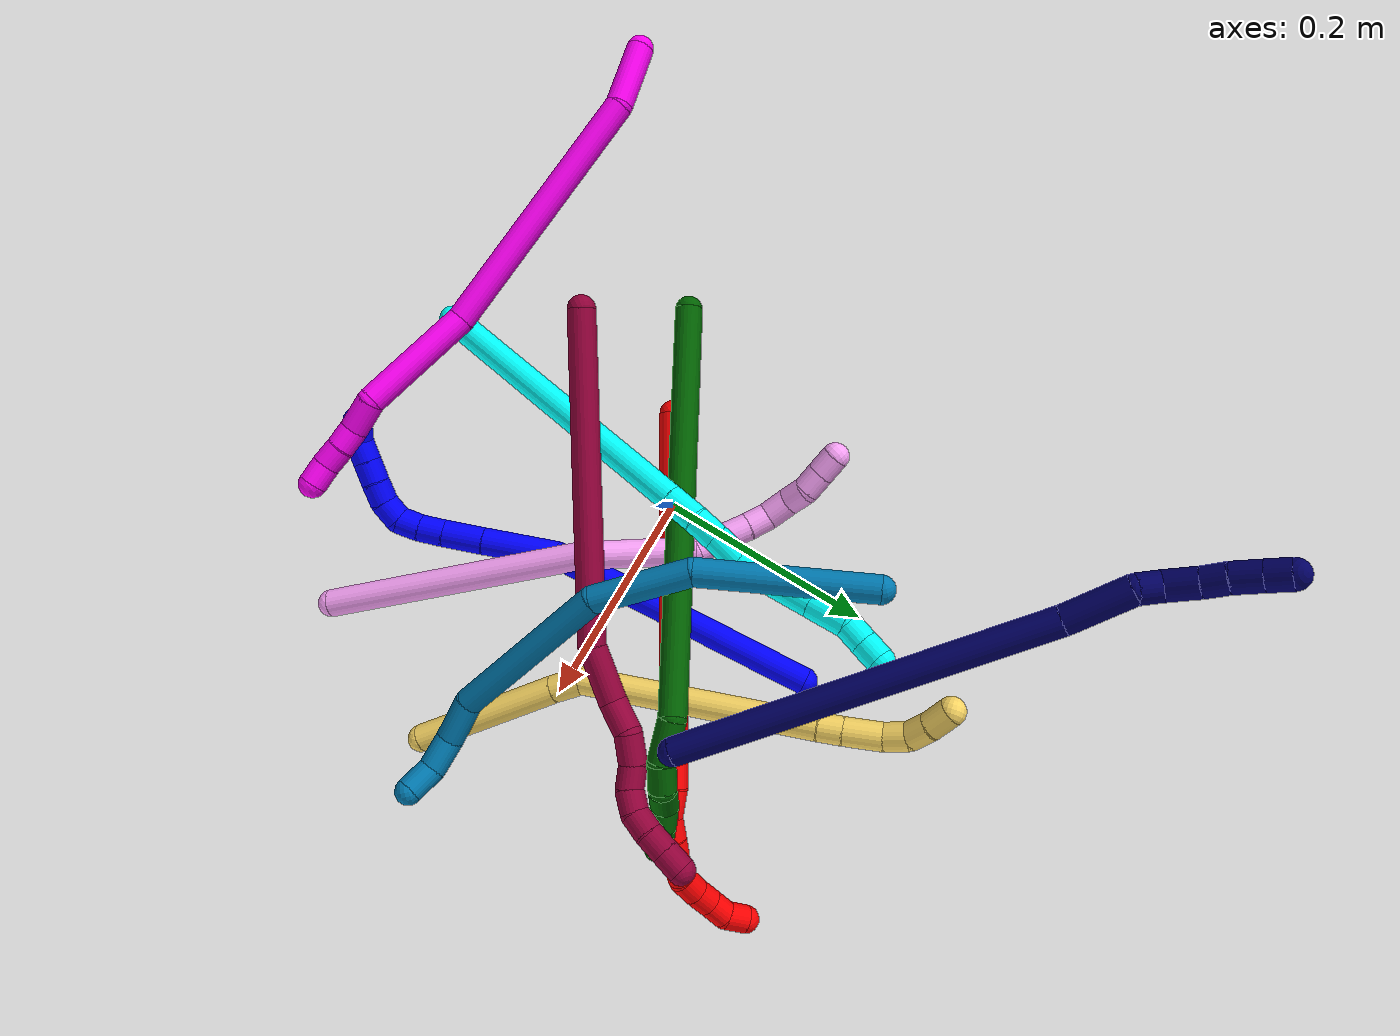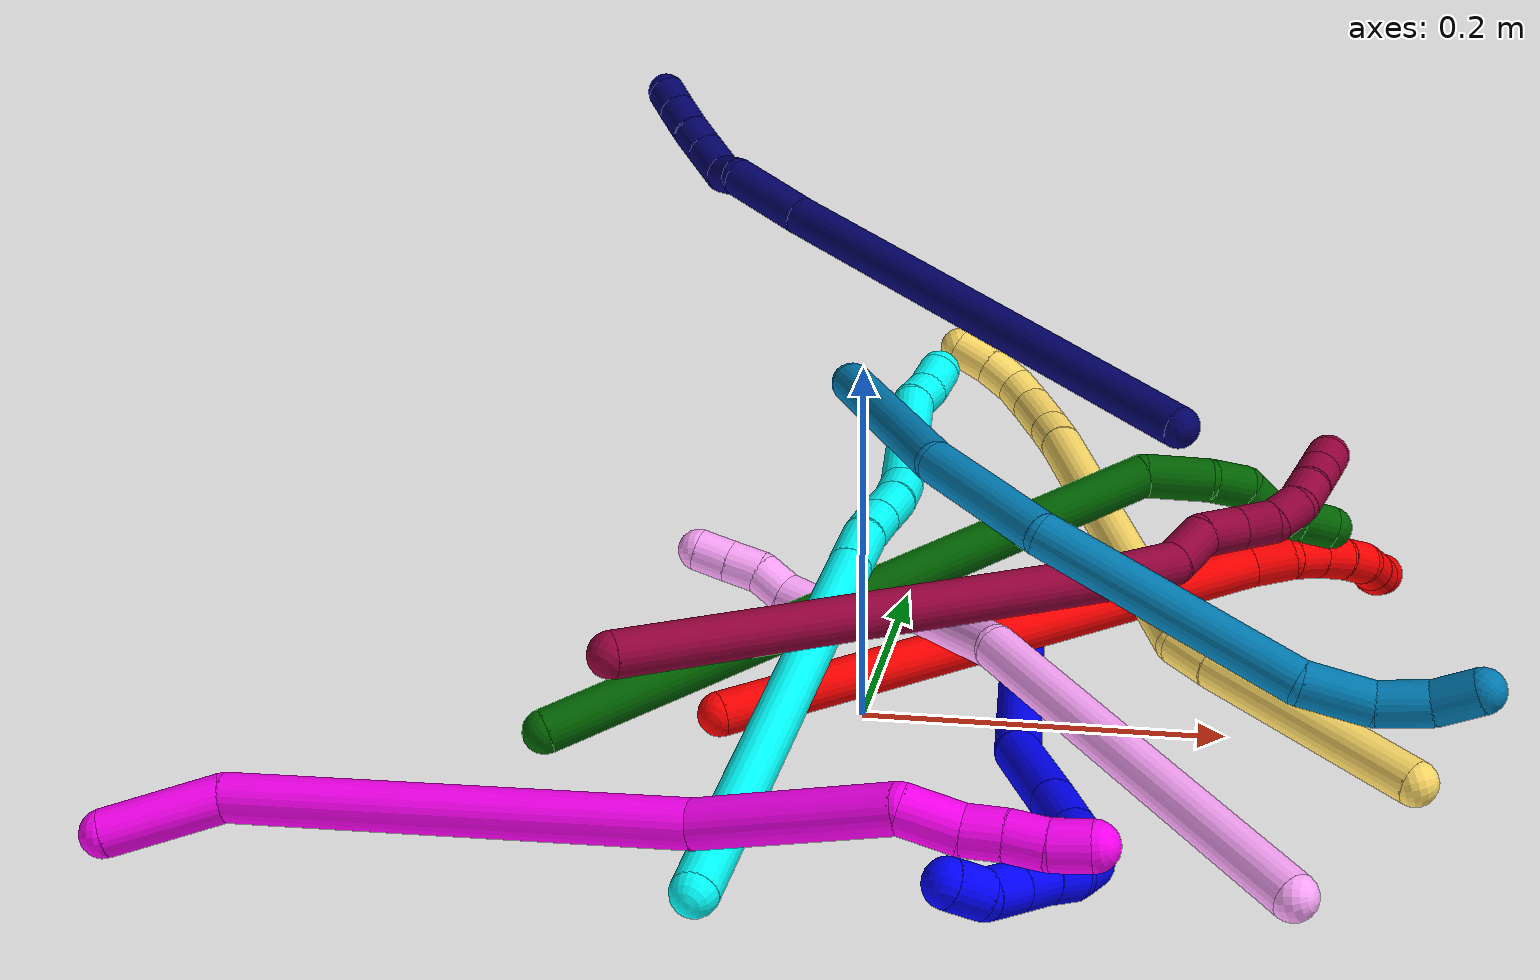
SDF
<sdf version="1.7">
 <world name="default">
  <plugin name="TubeGeneratorPlugin" filename="libtube_generator_plugin.so"/>
  <model name="photoneo_s_sensor">
   <static>1</static>
   <pose>0 0 2 1.57079 1.57079 3.14159</pose>
   <link name="link">
    <inertial><mass>0.1</mass></inertial>
    <sensor name="sensor" type="depth">
     <update_rate>30</update_rate>
     <camera>
      <horizontal_fov>1.22</horizontal_fov>
      <image><width>1920</width><height>1200</height><format>B8G8R8</format></image>
      <clip><near>0.1</near><far>2</far></clip>
      <depth_camera><output>points</output></depth_camera>
     </camera>
     <plugin name="camera_plugin" filename="libgazebo_ros_depth_camera.so">
      <baseline>0.2</baseline>
      <alwaysOn>1</alwaysOn>
      <updateRate>0.0</updateRate>
      <cameraName>camera_ir</cameraName>
      <imageTopicName>/camera/color/image_raw</imageTopicName>
      <cameraInfoTopicName>/camera/color/camera_info</cameraInfoTopicName>
      <depthImageTopicName>/camera/depth/image_raw</depthImageTopicName>
      <depthImageCameraInfoTopicName>/camera/depth/camera_info</depthImageCameraInfoTopicName>
      <pointCloudTopicName>/camera/depth/points</pointCloudTopicName>
      <frameName>fr_optical</frameName>
      <pointCloudCutoff>0.1</pointCloudCutoff>
      <pointCloudCutoffMax>2.0</pointCloudCutoffMax>
      <distortionK1>0</distortionK1>
      <distortionK2>0</distortionK2>
      <distortionK3>0</distortionK3>
      <distortionT1>0</distortionT1>
      <distortionT2>0</distortionT2>
      <CxPrime>0</CxPrime>
      <Cx>0</Cx>
      <Cy>0</Cy>
      <focalLength>0</focalLength>
      <hackBaseline>0</hackBaseline>
     </plugin>
    </sensor>
   </link>
  </model>
  <gravity>0 0 -9.8</gravity>
  <magnetic_field>6e-06 2.3e-05 -4.2e-05</magnetic_field>
  <atmosphere type="adiabatic"/>
  <physics name="default_physics" default="0" type="ode">
   <max_step_size>0.003</max_step_size>
   <real_time_factor>1</real_time_factor>
   <real_time_update_rate>1000</real_time_update_rate>
   <max_contacts>10000</max_contacts>
   <ode>
    <solver>
     <type>quick</type>
     <iters>100</iters>
     <sor>1.3</sor>
     <use_dynamic_moi_rescaling>0</use_dynamic_moi_rescaling>
    </solver>
    <constraints>
     <contact_max_correcting_vel>0</contact_max_correcting_vel>
     <contact_surface_layer>0.001</contact_surface_layer>
     <cfm>0</cfm>
     <erp>0.2</erp>
    </constraints>
   </ode>
  </physics>
  <scene><ambient>0.4 0.4 0.4 1</ambient><background>0.7 0.7 0.7 1</background><shadows>0</shadows></scene>
  <audio><device>default</device></audio>
  <spherical_coordinates>
   <surface_model>EARTH_WGS84</surface_model>
   <latitude_deg>0</latitude_deg>
   <longitude_deg>0</longitude_deg>
   <elevation>0</elevation>
   <heading_deg>0</heading_deg>
  </spherical_coordinates>
  <model name="bin">
   <static>1</static>
   <link name="bottom">
    <collision name="collision-bottom">
     <pose>0 0 -0.01 0 -0 0</pose>
     <geometry><box><size>0.8 0.6 0.02</size></box></geometry>
     <surface>
      <friction><ode><mu>100</mu><mu2>100</mu2></ode></friction>
      <contact><collide_bitmask>65535</collide_bitmask></contact>
     </surface>
    </collision>
   </link>
   <link name="west_wall">
    <collision name="collision-west_wall">
     <pose>-0.41 0 0.1 0 -0 0</pose>
     <geometry><box><size>0.02 0.6 0.2</size></box></geometry>
     <surface>
      <friction><ode><mu>100</mu><mu2>100</mu2></ode></friction>
      <contact><collide_bitmask>65535</collide_bitmask></contact>
     </surface>
    </collision>
   </link>
   <link name="east_wall">
    <collision name="collision-east_wall">
     <pose>0.41 0 0.1 0 -0 0</pose>
     <geometry><box><size>0.02 0.6 0.2</size></box></geometry>
     <surface>
      <friction><ode><mu>100</mu><mu2>100</mu2></ode></friction>
      <contact><collide_bitmask>65535</collide_bitmask></contact>
     </surface>
    </collision>
   </link>
   <link name="south_wall">
    <collision name="collision-south_wall">
     <pose>0 -0.31 0.1 0 -0 0</pose>
     <geometry><box><size>0.8 0.02 0.2</size></box></geometry>
     <surface>
      <friction><ode><mu>100</mu><mu2>100</mu2></ode></friction>
      <contact><collide_bitmask>65535</collide_bitmask></contact>
     </surface>
    </collision>
   </link>
   <link name="north_wall">
    <collision name="collision-north_wall">
     <pose>0 0.31 0.1 0 -0 0</pose>
     <geometry><box><size>0.8 0.02 0.2</size></box></geometry>
     <surface>
      <friction><ode><mu>100</mu><mu2>100</mu2></ode></friction>
      <contact><collide_bitmask>65535</collide_bitmask></contact>
     </surface>
    </collision>
   </link>
  </model>
  <model name="1">
   <static>0</static>
   <link name="1">
    <collision name="collision-cylinder-e_1_1_4">
     <pose>0.031042 -0.114692 -0.042599 1.92642 0.248477 0.355412</pose>
     <geometry><cylinder><radius>0.0125</radius><length>0.252449</length></cylinder></geometry>
     <surface>
      <friction><ode><mu>1.16</mu><mu2>1.16</mu2><slip1>0</slip1><slip2>0</slip2></ode></friction>
      <contact><ode><kp>1e+06</kp><kd>1</kd><max_vel>0</max_vel><min_depth>0.001</min_depth></ode></contact>
     </surface>
    </collision>
    <visual name="visual-cylinder-e_1_1_4">
     <pose>0.031042 -0.114692 -0.042599 1.92642 0.248477 0.355412</pose>
     <geometry><cylinder><radius>0.0125</radius><length>0.252449</length></cylinder></geometry>
     <material><ambient>0 0 1 1</ambient></material>
    </visual>
    <collision name="collision-cylinder-e_2_4_5">
     <pose>0.079162 -0.257807 -0.093272 1.84757 0.524077 0.682253</pose>
     <geometry><cylinder><radius>0.0125</radius><length>0.068256</length></cylinder></geometry>
     <surface>
      <friction><ode><mu>1.16</mu><mu2>1.16</mu2><slip1>0</slip1><slip2>0</slip2></ode></friction>
      <contact><ode><kp>1e+06</kp><kd>1</kd><max_vel>0</max_vel><min_depth>0.001</min_depth></ode></contact>
     </surface>
    </collision>
    <visual name="visual-cylinder-e_2_4_5">
     <pose>0.079162 -0.257807 -0.093272 1.84757 0.524077 0.682253</pose>
     <geometry><cylinder><radius>0.0125</radius><length>0.068256</length></cylinder></geometry>
     <material><ambient>0 0 1 1</ambient></material>
    </visual>
    <collision name="collision-cylinder-e_3_5_6">
     <pose>0.105339 -0.301382 -0.105993 1.86837 0.521194 0.692347</pose>
     <geometry><cylinder><radius>0.0125</radius><length>0.036549</length></cylinder></geometry>
     <surface>
      <friction><ode><mu>1.16</mu><mu2>1.16</mu2><slip1>0</slip1><slip2>0</slip2></ode></friction>
      <contact><ode><kp>1e+06</kp><kd>1</kd><max_vel>0</max_vel><min_depth>0.001</min_depth></ode></contact>
     </surface>
    </collision>
    <visual name="visual-cylinder-e_3_5_6">
     <pose>0.105339 -0.301382 -0.105993 1.86837 0.521194 0.692347</pose>
     <geometry><cylinder><radius>0.0125</radius><length>0.036549</length></cylinder></geometry>
     <material><ambient>0 0 1 1</ambient></material>
    </visual>
    <collision name="collision-cylinder-e_4_6_7">
     <pose>0.11963 -0.326006 -0.113318 1.84645 0.485324 0.632567</pose>
     <geometry><cylinder><radius>0.0125</radius><length>0.022258</length></cylinder></geometry>
     <surface>
      <friction><ode><mu>1.16</mu><mu2>1.16</mu2><slip1>0</slip1><slip2>0</slip2></ode></friction>
      <contact><ode><kp>1e+06</kp><kd>1</kd><max_vel>0</max_vel><min_depth>0.001</min_depth></ode></contact>
     </surface>
    </collision>
    <visual name="visual-cylinder-e_4_6_7">
     <pose>0.11963 -0.326006 -0.113318 1.84645 0.485324 0.632567</pose>
     <geometry><cylinder><radius>0.0125</radius><length>0.022258</length></cylinder></geometry>
     <material><ambient>0 0 1 1</ambient></material>
    </visual>
    <collision name="collision-cylinder-e_5_7_8">
     <pose>0.128069 -0.344711 -0.118357 1.82102 0.328425 0.420456</pose>
     <geometry><cylinder><radius>0.0125</radius><length>0.020137</length></cylinder></geometry>
     <surface>
      <friction><ode><mu>1.16</mu><mu2>1.16</mu2><slip1>0</slip1><slip2>0</slip2></ode></friction>
      <contact><ode><kp>1e+06</kp><kd>1</kd><max_vel>0</max_vel><min_depth>0.001</min_depth></ode></contact>
     </surface>
    </collision>
    <visual name="visual-cylinder-e_5_7_8">
     <pose>0.128069 -0.344711 -0.118357 1.82102 0.328425 0.420456</pose>
     <geometry><cylinder><radius>0.0125</radius><length>0.020137</length></cylinder></geometry>
     <material><ambient>0 0 1 1</ambient></material>
    </visual>
    <collision name="collision-cylinder-e_6_8_9">
     <pose>0.129515 -0.363404 -0.123972 1.90223 -0.178229 -0.249187</pose>
     <geometry><cylinder><radius>0.0125</radius><length>0.020329</length></cylinder></geometry>
     <surface>
      <friction><ode><mu>1.16</mu><mu2>1.16</mu2><slip1>0</slip1><slip2>0</slip2></ode></friction>
      <contact><ode><kp>1e+06</kp><kd>1</kd><max_vel>0</max_vel><min_depth>0.001</min_depth></ode></contact>
     </surface>
    </collision>
    <visual name="visual-cylinder-e_6_8_9">
     <pose>0.129515 -0.363404 -0.123972 1.90223 -0.178229 -0.249187</pose>
     <geometry><cylinder><radius>0.0125</radius><length>0.020329</length></cylinder></geometry>
     <material><ambient>0 0 1 1</ambient></material>
    </visual>
    <collision name="collision-cylinder-e_7_9_10">
     <pose>0.122829 -0.381319 -0.12939 1.82109 -0.510092 -0.647878</pose>
     <geometry><cylinder><radius>0.0125</radius><length>0.020003</length></cylinder></geometry>
     <surface>
      <friction><ode><mu>1.16</mu><mu2>1.16</mu2><slip1>0</slip1><slip2>0</slip2></ode></friction>
      <contact><ode><kp>1e+06</kp><kd>1</kd><max_vel>0</max_vel><min_depth>0.001</min_depth></ode></contact>
     </surface>
    </collision>
    <visual name="visual-cylinder-e_7_9_10">
     <pose>0.122829 -0.381319 -0.12939 1.82109 -0.510092 -0.647878</pose>
     <geometry><cylinder><radius>0.0125</radius><length>0.020003</length></cylinder></geometry>
     <material><ambient>0 0 1 1</ambient></material>
    </visual>
    <collision name="collision-cylinder-e_8_10_11">
     <pose>0.113048 -0.397939 -0.134643 1.93277 -0.511343 -0.723643</pose>
     <geometry><cylinder><radius>0.0125</radius><length>0.020019</length></cylinder></geometry>
     <surface>
      <friction><ode><mu>1.16</mu><mu2>1.16</mu2><slip1>0</slip1><slip2>0</slip2></ode></friction>
      <contact><ode><kp>1e+06</kp><kd>1</kd><max_vel>0</max_vel><min_depth>0.001</min_depth></ode></contact>
     </surface>
    </collision>
    <visual name="visual-cylinder-e_8_10_11">
     <pose>0.113048 -0.397939 -0.134643 1.93277 -0.511343 -0.723643</pose>
     <geometry><cylinder><radius>0.0125</radius><length>0.020019</length></cylinder></geometry>
     <material><ambient>0 0 1 1</ambient></material>
    </visual>
    <collision name="collision-cylinder-e_9_11_12">
     <pose>0.103268 -0.414298 -0.140734 1.92172 -0.510004 -0.714073</pose>
     <geometry><cylinder><radius>0.0125</radius><length>0.02</length></cylinder></geometry>
     <surface>
      <friction><ode><mu>1.16</mu><mu2>1.16</mu2><slip1>0</slip1><slip2>0</slip2></ode></friction>
      <contact><ode><kp>1e+06</kp><kd>1</kd><max_vel>0</max_vel><min_depth>0.001</min_depth></ode></contact>
     </surface>
    </collision>
    <visual name="visual-cylinder-e_9_11_12">
     <pose>0.103268 -0.414298 -0.140734 1.92172 -0.510004 -0.714073</pose>
     <geometry><cylinder><radius>0.0125</radius><length>0.02</length></cylinder></geometry>
     <material><ambient>0 0 1 1</ambient></material>
    </visual>
    <collision name="collision-cylinder-e_10_12_2">
     <pose>0.090672 -0.428832 -0.143155 1.47965 -0.880952 -0.812609</pose>
     <geometry><cylinder><radius>0.0125</radius><length>0.020001</length></cylinder></geometry>
     <surface>
      <friction><ode><mu>1.16</mu><mu2>1.16</mu2><slip1>0</slip1><slip2>0</slip2></ode></friction>
      <contact><ode><kp>1e+06</kp><kd>1</kd><max_vel>0</max_vel><min_depth>0.001</min_depth></ode></contact>
     </surface>
    </collision>
    <visual name="visual-cylinder-e_10_12_2">
     <pose>0.090672 -0.428832 -0.143155 1.47965 -0.880952 -0.812609</pose>
     <geometry><cylinder><radius>0.0125</radius><length>0.020001</length></cylinder></geometry>
     <material><ambient>0 0 1 1</ambient></material>
    </visual>
    <collision name="collision-sphere-2">
     <pose>0.082959 -0.43517 -0.142576 0 -0 0</pose>
     <geometry><sphere><radius>0.0125</radius></sphere></geometry>
     <surface>
      <friction><ode><mu>1.16</mu><mu2>1.16</mu2><slip1>0</slip1><slip2>0</slip2></ode></friction>
      <contact><ode><kp>1e+06</kp><kd>1</kd><max_vel>0</max_vel><min_depth>0.001</min_depth></ode></contact>
     </surface>
    </collision>
    <visual name="visual-sphere-2">
     <pose>0.082959 -0.43517 -0.142576 0 -0 0</pose>
     <geometry><sphere><radius>0.0125</radius></sphere></geometry>
     <material><ambient>0 0 1 1</ambient></material>
    </visual>
    <collision name="collision-sphere-12">
     <pose>0.098386 -0.422494 -0.143734 0 -0 0</pose>
     <geometry><sphere><radius>0.0125</radius></sphere></geometry>
     <surface>
      <friction><ode><mu>1.16</mu><mu2>1.16</mu2><slip1>0</slip1><slip2>0</slip2></ode></friction>
      <contact><ode><kp>1e+06</kp><kd>1</kd><max_vel>0</max_vel><min_depth>0.001</min_depth></ode></contact>
     </surface>
    </collision>
    <visual name="visual-sphere-12">
     <pose>0.098386 -0.422494 -0.143734 0 -0 0</pose>
     <geometry><sphere><radius>0.0125</radius></sphere></geometry>
     <material><ambient>0 0 1 1</ambient></material>
    </visual>
    <collision name="collision-sphere-11">
     <pose>0.10815 -0.406103 -0.137734 0 -0 0</pose>
     <geometry><sphere><radius>0.0125</radius></sphere></geometry>
     <surface>
      <friction><ode><mu>1.16</mu><mu2>1.16</mu2><slip1>0</slip1><slip2>0</slip2></ode></friction>
      <contact><ode><kp>1e+06</kp><kd>1</kd><max_vel>0</max_vel><min_depth>0.001</min_depth></ode></contact>
     </surface>
    </collision>
    <visual name="visual-sphere-11">
     <pose>0.10815 -0.406103 -0.137734 0 -0 0</pose>
     <geometry><sphere><radius>0.0125</radius></sphere></geometry>
     <material><ambient>0 0 1 1</ambient></material>
    </visual>
    <collision name="collision-sphere-10">
     <pose>0.117946 -0.389775 -0.131551 0 -0 0</pose>
     <geometry><sphere><radius>0.0125</radius></sphere></geometry>
     <surface>
      <friction><ode><mu>1.16</mu><mu2>1.16</mu2><slip1>0</slip1><slip2>0</slip2></ode></friction>
      <contact><ode><kp>1e+06</kp><kd>1</kd><max_vel>0</max_vel><min_depth>0.001</min_depth></ode></contact>
     </surface>
    </collision>
    <visual name="visual-sphere-10">
     <pose>0.117946 -0.389775 -0.131551 0 -0 0</pose>
     <geometry><sphere><radius>0.0125</radius></sphere></geometry>
     <material><ambient>0 0 1 1</ambient></material>
    </visual>
    <collision name="collision-sphere-9">
     <pose>0.127713 -0.372863 -0.127228 0 -0 0</pose>
     <geometry><sphere><radius>0.0125</radius></sphere></geometry>
     <surface>
      <friction><ode><mu>1.16</mu><mu2>1.16</mu2><slip1>0</slip1><slip2>0</slip2></ode></friction>
      <contact><ode><kp>1e+06</kp><kd>1</kd><max_vel>0</max_vel><min_depth>0.001</min_depth></ode></contact>
     </surface>
    </collision>
    <visual name="visual-sphere-9">
     <pose>0.127713 -0.372863 -0.127228 0 -0 0</pose>
     <geometry><sphere><radius>0.0125</radius></sphere></geometry>
     <material><ambient>0 0 1 1</ambient></material>
    </visual>
    <collision name="collision-sphere-4">
     <pose>0.062084 -0.229385 -0.085198 0 -0 0</pose>
     <geometry><sphere><radius>0.0125</radius></sphere></geometry>
     <surface>
      <friction><ode><mu>1.16</mu><mu2>1.16</mu2><slip1>0</slip1><slip2>0</slip2></ode></friction>
      <contact><ode><kp>1e+06</kp><kd>1</kd><max_vel>0</max_vel><min_depth>0.001</min_depth></ode></contact>
     </surface>
    </collision>
    <visual name="visual-sphere-4">
     <pose>0.062084 -0.229385 -0.085198 0 -0 0</pose>
     <geometry><sphere><radius>0.0125</radius></sphere></geometry>
     <material><ambient>0 0 1 1</ambient></material>
    </visual>
    <collision name="collision-sphere-1">
     <geometry><sphere><radius>0.0125</radius></sphere></geometry>
     <surface>
      <friction><ode><mu>1.16</mu><mu2>1.16</mu2><slip1>0</slip1><slip2>0</slip2></ode></friction>
      <contact><ode><kp>1e+06</kp><kd>1</kd><max_vel>0</max_vel><min_depth>0.001</min_depth></ode></contact>
     </surface>
    </collision>
    <visual name="visual-sphere-1">
     <geometry><sphere><radius>0.0125</radius></sphere></geometry>
     <material><ambient>0 0 1 1</ambient></material>
    </visual>
    <collision name="collision-sphere-8">
     <pose>0.131317 -0.353945 -0.120717 0 -0 0</pose>
     <geometry><sphere><radius>0.0125</radius></sphere></geometry>
     <surface>
      <friction><ode><mu>1.16</mu><mu2>1.16</mu2><slip1>0</slip1><slip2>0</slip2></ode></friction>
      <contact><ode><kp>1e+06</kp><kd>1</kd><max_vel>0</max_vel><min_depth>0.001</min_depth></ode></contact>
     </surface>
    </collision>
    <visual name="visual-sphere-8">
     <pose>0.131317 -0.353945 -0.120717 0 -0 0</pose>
     <geometry><sphere><radius>0.0125</radius></sphere></geometry>
     <material><ambient>0 0 1 1</ambient></material>
    </visual>
    <collision name="collision-sphere-5">
     <pose>0.09624 -0.28623 -0.101346 0 -0 0</pose>
     <geometry><sphere><radius>0.0125</radius></sphere></geometry>
     <surface>
      <friction><ode><mu>1.16</mu><mu2>1.16</mu2><slip1>0</slip1><slip2>0</slip2></ode></friction>
      <contact><ode><kp>1e+06</kp><kd>1</kd><max_vel>0</max_vel><min_depth>0.001</min_depth></ode></contact>
     </surface>
    </collision>
    <visual name="visual-sphere-5">
     <pose>0.09624 -0.28623 -0.101346 0 -0 0</pose>
     <geometry><sphere><radius>0.0125</radius></sphere></geometry>
     <material><ambient>0 0 1 1</ambient></material>
    </visual>
    <collision name="collision-sphere-6">
     <pose>0.114439 -0.316534 -0.110639 0 -0 0</pose>
     <geometry><sphere><radius>0.0125</radius></sphere></geometry>
     <surface>
      <friction><ode><mu>1.16</mu><mu2>1.16</mu2><slip1>0</slip1><slip2>0</slip2></ode></friction>
      <contact><ode><kp>1e+06</kp><kd>1</kd><max_vel>0</max_vel><min_depth>0.001</min_depth></ode></contact>
     </surface>
    </collision>
    <visual name="visual-sphere-6">
     <pose>0.114439 -0.316534 -0.110639 0 -0 0</pose>
     <geometry><sphere><radius>0.0125</radius></sphere></geometry>
     <material><ambient>0 0 1 1</ambient></material>
    </visual>
    <collision name="collision-sphere-7">
     <pose>0.124822 -0.335478 -0.115998 0 -0 0</pose>
     <geometry><sphere><radius>0.0125</radius></sphere></geometry>
     <surface>
      <friction><ode><mu>1.16</mu><mu2>1.16</mu2><slip1>0</slip1><slip2>0</slip2></ode></friction>
      <contact><ode><kp>1e+06</kp><kd>1</kd><max_vel>0</max_vel><min_depth>0.001</min_depth></ode></contact>
     </surface>
    </collision>
    <visual name="visual-sphere-7">
     <pose>0.124822 -0.335478 -0.115998 0 -0 0</pose>
     <geometry><sphere><radius>0.0125</radius></sphere></geometry>
     <material><ambient>0 0 1 1</ambient></material>
    </visual>
    <inertial>
     <pose>0.067127 -0.223216 -0.078763 0 -0 0</pose>
     <mass>0.5</mass>
     <inertia>
      <ixx>0.001737</ixx>
      <ixy>0</ixy>
      <ixz>0</ixz>
      <iyy>0.00011</iyy>
      <iyz>0</iyz>
      <izz>0.000906</izz>
     </inertia>
    </inertial>
   </link>
   <pose>0.074303 0.185953 0.011475 -0.400386 0.174281 -0.180521</pose>
  </model>
  <model name="2">
   <static>0</static>
   <link name="2">
    <collision name="collision-cylinder-e_1_1_4">
     <pose>0.104867 0.002203 0.130012 -0.016941 0.678677 -0.00598</pose>
     <geometry><cylinder><radius>0.0125</radius><length>0.334096</length></cylinder></geometry>
     <surface>
      <friction><ode><mu>1.16</mu><mu2>1.16</mu2><slip1>0</slip1><slip2>0</slip2></ode></friction>
      <contact><ode><kp>1e+06</kp><kd>1</kd><max_vel>0</max_vel><min_depth>0.001</min_depth></ode></contact>
     </surface>
    </collision>
    <visual name="visual-cylinder-e_1_1_4">
     <pose>0.104867 0.002203 0.130012 -0.016941 0.678677 -0.00598</pose>
     <geometry><cylinder><radius>0.0125</radius><length>0.334096</length></cylinder></geometry>
     <material><ambient>1 0 0 1</ambient></material>
    </visual>
    <collision name="collision-cylinder-e_2_4_5">
     <pose>0.219276 0.004368 0.268332 0.004474 0.854434 0.002037</pose>
     <geometry><cylinder><radius>0.0125</radius><length>0.025305</length></cylinder></geometry>
     <surface>
      <friction><ode><mu>1.16</mu><mu2>1.16</mu2><slip1>0</slip1><slip2>0</slip2></ode></friction>
      <contact><ode><kp>1e+06</kp><kd>1</kd><max_vel>0</max_vel><min_depth>0.001</min_depth></ode></contact>
     </surface>
    </collision>
    <visual name="visual-cylinder-e_2_4_5">
     <pose>0.219276 0.004368 0.268332 0.004474 0.854434 0.002037</pose>
     <geometry><cylinder><radius>0.0125</radius><length>0.025305</length></cylinder></geometry>
     <material><ambient>1 0 0 1</ambient></material>
    </visual>
    <collision name="collision-cylinder-e_3_5_6">
     <pose>0.233929 0.007128 0.284967 -0.324086 0.527002 -0.088146</pose>
     <geometry><cylinder><radius>0.0125</radius><length>0.020326</length></cylinder></geometry>
     <surface>
      <friction><ode><mu>1.16</mu><mu2>1.16</mu2><slip1>0</slip1><slip2>0</slip2></ode></friction>
      <contact><ode><kp>1e+06</kp><kd>1</kd><max_vel>0</max_vel><min_depth>0.001</min_depth></ode></contact>
     </surface>
    </collision>
    <visual name="visual-cylinder-e_3_5_6">
     <pose>0.233929 0.007128 0.284967 -0.324086 0.527002 -0.088146</pose>
     <geometry><cylinder><radius>0.0125</radius><length>0.020326</length></cylinder></geometry>
     <material><ambient>1 0 0 1</ambient></material>
    </visual>
    <collision name="collision-cylinder-e_4_6_7">
     <pose>0.244275 0.013539 0.301026 -0.437104 0.550148 -0.125202</pose>
     <geometry><cylinder><radius>0.0125</radius><length>0.020024</length></cylinder></geometry>
     <surface>
      <friction><ode><mu>1.16</mu><mu2>1.16</mu2><slip1>0</slip1><slip2>0</slip2></ode></friction>
      <contact><ode><kp>1e+06</kp><kd>1</kd><max_vel>0</max_vel><min_depth>0.001</min_depth></ode></contact>
     </surface>
    </collision>
    <visual name="visual-cylinder-e_4_6_7">
     <pose>0.244275 0.013539 0.301026 -0.437104 0.550148 -0.125202</pose>
     <geometry><cylinder><radius>0.0125</radius><length>0.020024</length></cylinder></geometry>
     <material><ambient>1 0 0 1</ambient></material>
    </visual>
    <collision name="collision-cylinder-e_5_7_8">
     <pose>0.253482 0.022159 0.316507 -0.573736 0.406576 -0.121472</pose>
     <geometry><cylinder><radius>0.0125</radius><length>0.02009</length></cylinder></geometry>
     <surface>
      <friction><ode><mu>1.16</mu><mu2>1.16</mu2><slip1>0</slip1><slip2>0</slip2></ode></friction>
      <contact><ode><kp>1e+06</kp><kd>1</kd><max_vel>0</max_vel><min_depth>0.001</min_depth></ode></contact>
     </surface>
    </collision>
    <visual name="visual-cylinder-e_5_7_8">
     <pose>0.253482 0.022159 0.316507 -0.573736 0.406576 -0.121472</pose>
     <geometry><cylinder><radius>0.0125</radius><length>0.02009</length></cylinder></geometry>
     <material><ambient>1 0 0 1</ambient></material>
    </visual>
    <collision name="collision-cylinder-e_6_8_9">
     <pose>0.25776 0.033569 0.331964 -0.693124 0.030496 -0.011014</pose>
     <geometry><cylinder><radius>0.0125</radius><length>0.020051</length></cylinder></geometry>
     <surface>
      <friction><ode><mu>1.16</mu><mu2>1.16</mu2><slip1>0</slip1><slip2>0</slip2></ode></friction>
      <contact><ode><kp>1e+06</kp><kd>1</kd><max_vel>0</max_vel><min_depth>0.001</min_depth></ode></contact>
     </surface>
    </collision>
    <visual name="visual-cylinder-e_6_8_9">
     <pose>0.25776 0.033569 0.331964 -0.693124 0.030496 -0.011014</pose>
     <geometry><cylinder><radius>0.0125</radius><length>0.020051</length></cylinder></geometry>
     <material><ambient>1 0 0 1</ambient></material>
    </visual>
    <collision name="collision-cylinder-e_7_9_10">
     <pose>0.257367 0.046128 0.347529 -0.664629 -0.069858 0.024117</pose>
     <geometry><cylinder><radius>0.0125</radius><length>0.02001</length></cylinder></geometry>
     <surface>
      <friction><ode><mu>1.16</mu><mu2>1.16</mu2><slip1>0</slip1><slip2>0</slip2></ode></friction>
      <contact><ode><kp>1e+06</kp><kd>1</kd><max_vel>0</max_vel><min_depth>0.001</min_depth></ode></contact>
     </surface>
    </collision>
    <visual name="visual-cylinder-e_7_9_10">
     <pose>0.257367 0.046128 0.347529 -0.664629 -0.069858 0.024117</pose>
     <geometry><cylinder><radius>0.0125</radius><length>0.02001</length></cylinder></geometry>
     <material><ambient>1 0 0 1</ambient></material>
    </visual>
    <collision name="collision-cylinder-e_8_10_11">
     <pose>0.255548 0.056885 0.364213 -0.480469 -0.112155 0.027501</pose>
     <geometry><cylinder><radius>0.0125</radius><length>0.020035</length></cylinder></geometry>
     <surface>
      <friction><ode><mu>1.16</mu><mu2>1.16</mu2><slip1>0</slip1><slip2>0</slip2></ode></friction>
      <contact><ode><kp>1e+06</kp><kd>1</kd><max_vel>0</max_vel><min_depth>0.001</min_depth></ode></contact>
     </surface>
    </collision>
    <visual name="visual-cylinder-e_8_10_11">
     <pose>0.255548 0.056885 0.364213 -0.480469 -0.112155 0.027501</pose>
     <geometry><cylinder><radius>0.0125</radius><length>0.020035</length></cylinder></geometry>
     <material><ambient>1 0 0 1</ambient></material>
    </visual>
    <collision name="collision-cylinder-e_9_11_2">
     <pose>0.249348 0.066287 0.380238 -0.588279 -0.53083 0.164317</pose>
     <geometry><cylinder><radius>0.0125</radius><length>0.020063</length></cylinder></geometry>
     <surface>
      <friction><ode><mu>1.16</mu><mu2>1.16</mu2><slip1>0</slip1><slip2>0</slip2></ode></friction>
      <contact><ode><kp>1e+06</kp><kd>1</kd><max_vel>0</max_vel><min_depth>0.001</min_depth></ode></contact>
     </surface>
    </collision>
    <visual name="visual-cylinder-e_9_11_2">
     <pose>0.249348 0.066287 0.380238 -0.588279 -0.53083 0.164317</pose>
     <geometry><cylinder><radius>0.0125</radius><length>0.020063</length></cylinder></geometry>
     <material><ambient>1 0 0 1</ambient></material>
    </visual>
    <collision name="collision-sphere-2">
     <pose>0.24427 0.071088 0.387434 0 -0 0</pose>
     <geometry><sphere><radius>0.0125</radius></sphere></geometry>
     <surface>
      <friction><ode><mu>1.16</mu><mu2>1.16</mu2><slip1>0</slip1><slip2>0</slip2></ode></friction>
      <contact><ode><kp>1e+06</kp><kd>1</kd><max_vel>0</max_vel><min_depth>0.001</min_depth></ode></contact>
     </surface>
    </collision>
    <visual name="visual-sphere-2">
     <pose>0.24427 0.071088 0.387434 0 -0 0</pose>
     <geometry><sphere><radius>0.0125</radius></sphere></geometry>
     <material><ambient>1 0 0 1</ambient></material>
    </visual>
    <collision name="collision-sphere-11">
     <pose>0.254427 0.061486 0.373041 0 -0 0</pose>
     <geometry><sphere><radius>0.0125</radius></sphere></geometry>
     <surface>
      <friction><ode><mu>1.16</mu><mu2>1.16</mu2><slip1>0</slip1><slip2>0</slip2></ode></friction>
      <contact><ode><kp>1e+06</kp><kd>1</kd><max_vel>0</max_vel><min_depth>0.001</min_depth></ode></contact>
     </surface>
    </collision>
    <visual name="visual-sphere-11">
     <pose>0.254427 0.061486 0.373041 0 -0 0</pose>
     <geometry><sphere><radius>0.0125</radius></sphere></geometry>
     <material><ambient>1 0 0 1</ambient></material>
    </visual>
    <collision name="collision-sphere-10">
     <pose>0.256669 0.052284 0.355385 0 -0 0</pose>
     <geometry><sphere><radius>0.0125</radius></sphere></geometry>
     <surface>
      <friction><ode><mu>1.16</mu><mu2>1.16</mu2><slip1>0</slip1><slip2>0</slip2></ode></friction>
      <contact><ode><kp>1e+06</kp><kd>1</kd><max_vel>0</max_vel><min_depth>0.001</min_depth></ode></contact>
     </surface>
    </collision>
    <visual name="visual-sphere-10">
     <pose>0.256669 0.052284 0.355385 0 -0 0</pose>
     <geometry><sphere><radius>0.0125</radius></sphere></geometry>
     <material><ambient>1 0 0 1</ambient></material>
    </visual>
    <collision name="collision-sphere-9">
     <pose>0.258066 0.039972 0.339673 0 -0 0</pose>
     <geometry><sphere><radius>0.0125</radius></sphere></geometry>
     <surface>
      <friction><ode><mu>1.16</mu><mu2>1.16</mu2><slip1>0</slip1><slip2>0</slip2></ode></friction>
      <contact><ode><kp>1e+06</kp><kd>1</kd><max_vel>0</max_vel><min_depth>0.001</min_depth></ode></contact>
     </surface>
    </collision>
    <visual name="visual-sphere-9">
     <pose>0.258066 0.039972 0.339673 0 -0 0</pose>
     <geometry><sphere><radius>0.0125</radius></sphere></geometry>
     <material><ambient>1 0 0 1</ambient></material>
    </visual>
    <collision name="collision-sphere-4">
     <pose>0.209733 0.004406 0.260024 0 -0 0</pose>
     <geometry><sphere><radius>0.0125</radius></sphere></geometry>
     <surface>
      <friction><ode><mu>1.16</mu><mu2>1.16</mu2><slip1>0</slip1><slip2>0</slip2></ode></friction>
      <contact><ode><kp>1e+06</kp><kd>1</kd><max_vel>0</max_vel><min_depth>0.001</min_depth></ode></contact>
     </surface>
    </collision>
    <visual name="visual-sphere-4">
     <pose>0.209733 0.004406 0.260024 0 -0 0</pose>
     <geometry><sphere><radius>0.0125</radius></sphere></geometry>
     <material><ambient>1 0 0 1</ambient></material>
    </visual>
    <collision name="collision-sphere-1">
     <geometry><sphere><radius>0.0125</radius></sphere></geometry>
     <surface>
      <friction><ode><mu>1.16</mu><mu2>1.16</mu2><slip1>0</slip1><slip2>0</slip2></ode></friction>
      <contact><ode><kp>1e+06</kp><kd>1</kd><max_vel>0</max_vel><min_depth>0.001</min_depth></ode></contact>
     </surface>
    </collision>
    <visual name="visual-sphere-1">
     <geometry><sphere><radius>0.0125</radius></sphere></geometry>
     <material><ambient>1 0 0 1</ambient></material>
    </visual>
    <collision name="collision-sphere-8">
     <pose>0.257454 0.027167 0.324255 0 -0 0</pose>
     <geometry><sphere><radius>0.0125</radius></sphere></geometry>
     <surface>
      <friction><ode><mu>1.16</mu><mu2>1.16</mu2><slip1>0</slip1><slip2>0</slip2></ode></friction>
      <contact><ode><kp>1e+06</kp><kd>1</kd><max_vel>0</max_vel><min_depth>0.001</min_depth></ode></contact>
     </surface>
    </collision>
    <visual name="visual-sphere-8">
     <pose>0.257454 0.027167 0.324255 0 -0 0</pose>
     <geometry><sphere><radius>0.0125</radius></sphere></geometry>
     <material><ambient>1 0 0 1</ambient></material>
    </visual>
    <collision name="collision-sphere-5">
     <pose>0.228818 0.004331 0.27664 0 -0 0</pose>
     <geometry><sphere><radius>0.0125</radius></sphere></geometry>
     <surface>
      <friction><ode><mu>1.16</mu><mu2>1.16</mu2><slip1>0</slip1><slip2>0</slip2></ode></friction>
      <contact><ode><kp>1e+06</kp><kd>1</kd><max_vel>0</max_vel><min_depth>0.001</min_depth></ode></contact>
     </surface>
    </collision>
    <visual name="visual-sphere-5">
     <pose>0.228818 0.004331 0.27664 0 -0 0</pose>
     <geometry><sphere><radius>0.0125</radius></sphere></geometry>
     <material><ambient>1 0 0 1</ambient></material>
    </visual>
    <collision name="collision-sphere-6">
     <pose>0.239041 0.009926 0.293293 0 -0 0</pose>
     <geometry><sphere><radius>0.0125</radius></sphere></geometry>
     <surface>
      <friction><ode><mu>1.16</mu><mu2>1.16</mu2><slip1>0</slip1><slip2>0</slip2></ode></friction>
      <contact><ode><kp>1e+06</kp><kd>1</kd><max_vel>0</max_vel><min_depth>0.001</min_depth></ode></contact>
     </surface>
    </collision>
    <visual name="visual-sphere-6">
     <pose>0.239041 0.009926 0.293293 0 -0 0</pose>
     <geometry><sphere><radius>0.0125</radius></sphere></geometry>
     <material><ambient>1 0 0 1</ambient></material>
    </visual>
    <collision name="collision-sphere-7">
     <pose>0.24951 0.017151 0.308758 0 -0 0</pose>
     <geometry><sphere><radius>0.0125</radius></sphere></geometry>
     <surface>
      <friction><ode><mu>1.16</mu><mu2>1.16</mu2><slip1>0</slip1><slip2>0</slip2></ode></friction>
      <contact><ode><kp>1e+06</kp><kd>1</kd><max_vel>0</max_vel><min_depth>0.001</min_depth></ode></contact>
     </surface>
    </collision>
    <visual name="visual-sphere-7">
     <pose>0.24951 0.017151 0.308758 0 -0 0</pose>
     <geometry><sphere><radius>0.0125</radius></sphere></geometry>
     <material><ambient>1 0 0 1</ambient></material>
    </visual>
    <inertial>
     <pose>0.151528 0.011547 0.193883 0 -0 0</pose>
     <mass>0.5</mass>
     <inertia>
      <ixx>0.002444</ixx>
      <ixy>0</ixy>
      <ixz>0</ixz>
      <iyy>0.003122</iyy>
      <iyz>0</iyz>
      <izz>-0.001978</izz>
     </inertia>
    </inertial>
   </link>
   <pose>-0.072448 -0.041795 0.012843 -1.37816 0.020181 -0.32964</pose>
  </model>
  <model name="3">
   <static>0</static>
   <link name="3">
    <collision name="collision-cylinder-e_1_1_4">
     <pose>0.006702 0.009259 -0.135247 -3.07324 0.049395 -1.25138</pose>
     <geometry><cylinder><radius>0.0125</radius><length>0.271458</length></cylinder></geometry>
     <surface>
      <friction><ode><mu>1.16</mu><mu2>1.16</mu2><slip1>0</slip1><slip2>0</slip2></ode></friction>
      <contact><ode><kp>1e+06</kp><kd>1</kd><max_vel>0</max_vel><min_depth>0.001</min_depth></ode></contact>
     </surface>
    </collision>
    <visual name="visual-cylinder-e_1_1_4">
     <pose>0.006702 0.009259 -0.135247 -3.07324 0.049395 -1.25138</pose>
     <geometry><cylinder><radius>0.0125</radius><length>0.271458</length></cylinder></geometry>
     <material><ambient>0.003922 1 0.996078 1</ambient></material>
    </visual>
    <collision name="collision-cylinder-e_2_4_5">
     <pose>0.014075 0.019547 -0.285481 -3.07299 0.04471 -1.15496</pose>
     <geometry><cylinder><radius>0.0125</radius><length>0.030076</length></cylinder></geometry>
     <surface>
      <friction><ode><mu>1.16</mu><mu2>1.16</mu2><slip1>0</slip1><slip2>0</slip2></ode></friction>
      <contact><ode><kp>1e+06</kp><kd>1</kd><max_vel>0</max_vel><min_depth>0.001</min_depth></ode></contact>
     </surface>
    </collision>
    <visual name="visual-cylinder-e_2_4_5">
     <pose>0.014075 0.019547 -0.285481 -3.07299 0.04471 -1.15496</pose>
     <geometry><cylinder><radius>0.0125</radius><length>0.030076</length></cylinder></geometry>
     <material><ambient>0.003922 1 0.996078 1</ambient></material>
    </visual>
    <collision name="collision-cylinder-e_3_5_6">
     <pose>0.01336 0.021485 -0.312041 -3.06327 -0.118963 1.97774</pose>
     <geometry><cylinder><radius>0.0125</radius><length>0.02338</length></cylinder></geometry>
     <surface>
      <friction><ode><mu>1.16</mu><mu2>1.16</mu2><slip1>0</slip1><slip2>0</slip2></ode></friction>
      <contact><ode><kp>1e+06</kp><kd>1</kd><max_vel>0</max_vel><min_depth>0.001</min_depth></ode></contact>
     </surface>
    </collision>
    <visual name="visual-cylinder-e_3_5_6">
     <pose>0.01336 0.021485 -0.312041 -3.06327 -0.118963 1.97774</pose>
     <geometry><cylinder><radius>0.0125</radius><length>0.02338</length></cylinder></geometry>
     <material><ambient>0.003922 1 0.996078 1</ambient></material>
    </visual>
    <collision name="collision-cylinder-e_4_6_7">
     <pose>0.010038 0.023231 -0.336959 -3.0789 -0.143687 2.31985</pose>
     <geometry><cylinder><radius>0.0125</radius><length>0.027025</length></cylinder></geometry>
     <surface>
      <friction><ode><mu>1.16</mu><mu2>1.16</mu2><slip1>0</slip1><slip2>0</slip2></ode></friction>
      <contact><ode><kp>1e+06</kp><kd>1</kd><max_vel>0</max_vel><min_depth>0.001</min_depth></ode></contact>
     </surface>
    </collision>
    <visual name="visual-cylinder-e_4_6_7">
     <pose>0.010038 0.023231 -0.336959 -3.0789 -0.143687 2.31985</pose>
     <geometry><cylinder><radius>0.0125</radius><length>0.027025</length></cylinder></geometry>
     <material><ambient>0.003922 1 0.996078 1</ambient></material>
    </visual>
    <collision name="collision-cylinder-e_5_7_8">
     <pose>0.00718 0.026357 -0.361125 -2.93321 -0.083283 0.758316</pose>
     <geometry><cylinder><radius>0.0125</radius><length>0.022194</length></cylinder></geometry>
     <surface>
      <friction><ode><mu>1.16</mu><mu2>1.16</mu2><slip1>0</slip1><slip2>0</slip2></ode></friction>
      <contact><ode><kp>1e+06</kp><kd>1</kd><max_vel>0</max_vel><min_depth>0.001</min_depth></ode></contact>
     </surface>
    </collision>
    <visual name="visual-cylinder-e_5_7_8">
     <pose>0.00718 0.026357 -0.361125 -2.93321 -0.083283 0.758316</pose>
     <geometry><cylinder><radius>0.0125</radius><length>0.022194</length></cylinder></geometry>
     <material><ambient>0.003922 1 0.996078 1</ambient></material>
    </visual>
    <collision name="collision-cylinder-e_6_8_9">
     <pose>0.010291 0.0338 -0.396383 -2.93366 0.16015 -1.3112</pose>
     <geometry><cylinder><radius>0.0125</radius><length>0.050599</length></cylinder></geometry>
     <surface>
      <friction><ode><mu>1.16</mu><mu2>1.16</mu2><slip1>0</slip1><slip2>0</slip2></ode></friction>
      <contact><ode><kp>1e+06</kp><kd>1</kd><max_vel>0</max_vel><min_depth>0.001</min_depth></ode></contact>
     </surface>
    </collision>
    <visual name="visual-cylinder-e_6_8_9">
     <pose>0.010291 0.0338 -0.396383 -2.93366 0.16015 -1.3112</pose>
     <geometry><cylinder><radius>0.0125</radius><length>0.050599</length></cylinder></geometry>
     <material><ambient>0.003922 1 0.996078 1</ambient></material>
    </visual>
    <collision name="collision-cylinder-e_7_9_10">
     <pose>0.017281 0.042384 -0.437368 -2.93732 0.173117 -1.40508</pose>
     <geometry><cylinder><radius>0.0125</radius><length>0.034312</length></cylinder></geometry>
     <surface>
      <friction><ode><mu>1.16</mu><mu2>1.16</mu2><slip1>0</slip1><slip2>0</slip2></ode></friction>
      <contact><ode><kp>1e+06</kp><kd>1</kd><max_vel>0</max_vel><min_depth>0.001</min_depth></ode></contact>
     </surface>
    </collision>
    <visual name="visual-cylinder-e_7_9_10">
     <pose>0.017281 0.042384 -0.437368 -2.93732 0.173117 -1.40508</pose>
     <geometry><cylinder><radius>0.0125</radius><length>0.034312</length></cylinder></geometry>
     <material><ambient>0.003922 1 0.996078 1</ambient></material>
    </visual>
    <collision name="collision-cylinder-e_8_10_11">
     <pose>0.018685 0.045591 -0.463955 3.1195 -0.153231 -2.85574</pose>
     <geometry><cylinder><radius>0.0125</radius><length>0.02032</length></cylinder></geometry>
     <surface>
      <friction><ode><mu>1.16</mu><mu2>1.16</mu2><slip1>0</slip1><slip2>0</slip2></ode></friction>
      <contact><ode><kp>1e+06</kp><kd>1</kd><max_vel>0</max_vel><min_depth>0.001</min_depth></ode></contact>
     </surface>
    </collision>
    <visual name="visual-cylinder-e_8_10_11">
     <pose>0.018685 0.045591 -0.463955 3.1195 -0.153231 -2.85574</pose>
     <geometry><cylinder><radius>0.0125</radius><length>0.02032</length></cylinder></geometry>
     <material><ambient>0.003922 1 0.996078 1</ambient></material>
    </visual>
    <collision name="collision-cylinder-e_9_11_2">
     <pose>0.018121 0.044268 -0.484205 3.03421 0.09577 1.45636</pose>
     <geometry><cylinder><radius>0.0125</radius><length>0.020637</length></cylinder></geometry>
     <surface>
      <friction><ode><mu>1.16</mu><mu2>1.16</mu2><slip1>0</slip1><slip2>0</slip2></ode></friction>
      <contact><ode><kp>1e+06</kp><kd>1</kd><max_vel>0</max_vel><min_depth>0.001</min_depth></ode></contact>
     </surface>
    </collision>
    <visual name="visual-cylinder-e_9_11_2">
     <pose>0.018121 0.044268 -0.484205 3.03421 0.09577 1.45636</pose>
     <geometry><cylinder><radius>0.0125</radius><length>0.020637</length></cylinder></geometry>
     <material><ambient>0.003922 1 0.996078 1</ambient></material>
    </visual>
    <collision name="collision-sphere-2">
     <pose>0.019108 0.043167 -0.494417 0 -0 0</pose>
     <geometry><sphere><radius>0.0125</radius></sphere></geometry>
     <surface>
      <friction><ode><mu>1.16</mu><mu2>1.16</mu2><slip1>0</slip1><slip2>0</slip2></ode></friction>
      <contact><ode><kp>1e+06</kp><kd>1</kd><max_vel>0</max_vel><min_depth>0.001</min_depth></ode></contact>
     </surface>
    </collision>
    <visual name="visual-sphere-2">
     <pose>0.019108 0.043167 -0.494417 0 -0 0</pose>
     <geometry><sphere><radius>0.0125</radius></sphere></geometry>
     <material><ambient>0.003922 1 0.996078 1</ambient></material>
    </visual>
    <collision name="collision-sphere-11">
     <pose>0.017134 0.045369 -0.473993 0 -0 0</pose>
     <geometry><sphere><radius>0.0125</radius></sphere></geometry>
     <surface>
      <friction><ode><mu>1.16</mu><mu2>1.16</mu2><slip1>0</slip1><slip2>0</slip2></ode></friction>
      <contact><ode><kp>1e+06</kp><kd>1</kd><max_vel>0</max_vel><min_depth>0.001</min_depth></ode></contact>
     </surface>
    </collision>
    <visual name="visual-sphere-11">
     <pose>0.017134 0.045369 -0.473993 0 -0 0</pose>
     <geometry><sphere><radius>0.0125</radius></sphere></geometry>
     <material><ambient>0.003922 1 0.996078 1</ambient></material>
    </visual>
    <collision name="collision-sphere-10">
     <pose>0.020236 0.045813 -0.453916 0 -0 0</pose>
     <geometry><sphere><radius>0.0125</radius></sphere></geometry>
     <surface>
      <friction><ode><mu>1.16</mu><mu2>1.16</mu2><slip1>0</slip1><slip2>0</slip2></ode></friction>
      <contact><ode><kp>1e+06</kp><kd>1</kd><max_vel>0</max_vel><min_depth>0.001</min_depth></ode></contact>
     </surface>
    </collision>
    <visual name="visual-sphere-10">
     <pose>0.020236 0.045813 -0.453916 0 -0 0</pose>
     <geometry><sphere><radius>0.0125</radius></sphere></geometry>
     <material><ambient>0.003922 1 0.996078 1</ambient></material>
    </visual>
    <collision name="collision-sphere-9">
     <pose>0.014326 0.038956 -0.42082 0 -0 0</pose>
     <geometry><sphere><radius>0.0125</radius></sphere></geometry>
     <surface>
      <friction><ode><mu>1.16</mu><mu2>1.16</mu2><slip1>0</slip1><slip2>0</slip2></ode></friction>
      <contact><ode><kp>1e+06</kp><kd>1</kd><max_vel>0</max_vel><min_depth>0.001</min_depth></ode></contact>
     </surface>
    </collision>
    <visual name="visual-sphere-9">
     <pose>0.014326 0.038956 -0.42082 0 -0 0</pose>
     <geometry><sphere><radius>0.0125</radius></sphere></geometry>
     <material><ambient>0.003922 1 0.996078 1</ambient></material>
    </visual>
    <collision name="collision-sphere-4">
     <pose>0.013403 0.018517 -0.270494 0 -0 0</pose>
     <geometry><sphere><radius>0.0125</radius></sphere></geometry>
     <surface>
      <friction><ode><mu>1.16</mu><mu2>1.16</mu2><slip1>0</slip1><slip2>0</slip2></ode></friction>
      <contact><ode><kp>1e+06</kp><kd>1</kd><max_vel>0</max_vel><min_depth>0.001</min_depth></ode></contact>
     </surface>
    </collision>
    <visual name="visual-sphere-4">
     <pose>0.013403 0.018517 -0.270494 0 -0 0</pose>
     <geometry><sphere><radius>0.0125</radius></sphere></geometry>
     <material><ambient>0.003922 1 0.996078 1</ambient></material>
    </visual>
    <collision name="collision-sphere-1">
     <geometry><sphere><radius>0.0125</radius></sphere></geometry>
     <surface>
      <friction><ode><mu>1.16</mu><mu2>1.16</mu2><slip1>0</slip1><slip2>0</slip2></ode></friction>
      <contact><ode><kp>1e+06</kp><kd>1</kd><max_vel>0</max_vel><min_depth>0.001</min_depth></ode></contact>
     </surface>
    </collision>
    <visual name="visual-sphere-1">
     <geometry><sphere><radius>0.0125</radius></sphere></geometry>
     <material><ambient>0.003922 1 0.996078 1</ambient></material>
    </visual>
    <collision name="collision-sphere-8">
     <pose>0.006257 0.028644 -0.371945 0 -0 0</pose>
     <geometry><sphere><radius>0.0125</radius></sphere></geometry>
     <surface>
      <friction><ode><mu>1.16</mu><mu2>1.16</mu2><slip1>0</slip1><slip2>0</slip2></ode></friction>
      <contact><ode><kp>1e+06</kp><kd>1</kd><max_vel>0</max_vel><min_depth>0.001</min_depth></ode></contact>
     </surface>
    </collision>
    <visual name="visual-sphere-8">
     <pose>0.006257 0.028644 -0.371945 0 -0 0</pose>
     <geometry><sphere><radius>0.0125</radius></sphere></geometry>
     <material><ambient>0.003922 1 0.996078 1</ambient></material>
    </visual>
    <collision name="collision-sphere-5">
     <pose>0.014747 0.020577 -0.300469 0 -0 0</pose>
     <geometry><sphere><radius>0.0125</radius></sphere></geometry>
     <surface>
      <friction><ode><mu>1.16</mu><mu2>1.16</mu2><slip1>0</slip1><slip2>0</slip2></ode></friction>
      <contact><ode><kp>1e+06</kp><kd>1</kd><max_vel>0</max_vel><min_depth>0.001</min_depth></ode></contact>
     </surface>
    </collision>
    <visual name="visual-sphere-5">
     <pose>0.014747 0.020577 -0.300469 0 -0 0</pose>
     <geometry><sphere><radius>0.0125</radius></sphere></geometry>
     <material><ambient>0.003922 1 0.996078 1</ambient></material>
    </visual>
    <collision name="collision-sphere-6">
     <pose>0.011973 0.022393 -0.323613 0 -0 0</pose>
     <geometry><sphere><radius>0.0125</radius></sphere></geometry>
     <surface>
      <friction><ode><mu>1.16</mu><mu2>1.16</mu2><slip1>0</slip1><slip2>0</slip2></ode></friction>
      <contact><ode><kp>1e+06</kp><kd>1</kd><max_vel>0</max_vel><min_depth>0.001</min_depth></ode></contact>
     </surface>
    </collision>
    <visual name="visual-sphere-6">
     <pose>0.011973 0.022393 -0.323613 0 -0 0</pose>
     <geometry><sphere><radius>0.0125</radius></sphere></geometry>
     <material><ambient>0.003922 1 0.996078 1</ambient></material>
    </visual>
    <collision name="collision-sphere-7">
     <pose>0.008103 0.024069 -0.350306 0 -0 0</pose>
     <geometry><sphere><radius>0.0125</radius></sphere></geometry>
     <surface>
      <friction><ode><mu>1.16</mu><mu2>1.16</mu2><slip1>0</slip1><slip2>0</slip2></ode></friction>
      <contact><ode><kp>1e+06</kp><kd>1</kd><max_vel>0</max_vel><min_depth>0.001</min_depth></ode></contact>
     </surface>
    </collision>
    <visual name="visual-sphere-7">
     <pose>0.008103 0.024069 -0.350306 0 -0 0</pose>
     <geometry><sphere><radius>0.0125</radius></sphere></geometry>
     <material><ambient>0.003922 1 0.996078 1</ambient></material>
    </visual>
    <inertial>
     <pose>0.009706 0.019642 -0.2484 0 -0 0</pose>
     <mass>0.5</mass>
     <inertia>
      <ixx>-0.001074</ixx>
      <ixy>0</ixy>
      <ixz>0</ixz>
      <iyy>-0.002123</iyy>
      <iyz>0</iyz>
      <izz>-0.000242</izz>
     </inertia>
    </inertial>
   </link>
   <pose>-0.042472 -0.258655 0.011494 -2.17988 -1.09638 -2.8067</pose>
  </model>
  <model name="4">
   <static>0</static>
   <link name="4">
    <collision name="collision-cylinder-e_1_1_4">
     <pose>-0.049683 0.053261 -0.096248 -2.63617 -0.424229 1.39021</pose>
     <geometry><cylinder><radius>0.0125</radius><length>0.241402</length></cylinder></geometry>
     <surface>
      <friction><ode><mu>1.16</mu><mu2>1.16</mu2><slip1>0</slip1><slip2>0</slip2></ode></friction>
      <contact><ode><kp>1e+06</kp><kd>1</kd><max_vel>0</max_vel><min_depth>0.001</min_depth></ode></contact>
     </surface>
    </collision>
    <visual name="visual-cylinder-e_1_1_4">
     <pose>-0.049683 0.053261 -0.096248 -2.63617 -0.424229 1.39021</pose>
     <geometry><cylinder><radius>0.0125</radius><length>0.241402</length></cylinder></geometry>
     <material><ambient>1 0.65098 0.996078 1</ambient></material>
    </visual>
    <collision name="collision-cylinder-e_2_4_5">
     <pose>-0.104385 0.136502 -0.232962 -2.50394 -0.099343 0.298962</pose>
     <geometry><cylinder><radius>0.0125</radius><length>0.101224</length></cylinder></geometry>
     <surface>
      <friction><ode><mu>1.16</mu><mu2>1.16</mu2><slip1>0</slip1><slip2>0</slip2></ode></friction>
      <contact><ode><kp>1e+06</kp><kd>1</kd><max_vel>0</max_vel><min_depth>0.001</min_depth></ode></contact>
     </surface>
    </collision>
    <visual name="visual-cylinder-e_2_4_5">
     <pose>-0.104385 0.136502 -0.232962 -2.50394 -0.099343 0.298962</pose>
     <geometry><cylinder><radius>0.0125</radius><length>0.101224</length></cylinder></geometry>
     <material><ambient>1 0.65098 0.996078 1</ambient></material>
    </visual>
    <collision name="collision-cylinder-e_3_5_6">
     <pose>-0.10721 0.17012 -0.287557 -2.88964 0.149347 -1.06713</pose>
     <geometry><cylinder><radius>0.0125</radius><length>0.029508</length></cylinder></geometry>
     <surface>
      <friction><ode><mu>1.16</mu><mu2>1.16</mu2><slip1>0</slip1><slip2>0</slip2></ode></friction>
      <contact><ode><kp>1e+06</kp><kd>1</kd><max_vel>0</max_vel><min_depth>0.001</min_depth></ode></contact>
     </surface>
    </collision>
    <visual name="visual-cylinder-e_3_5_6">
     <pose>-0.10721 0.17012 -0.287557 -2.88964 0.149347 -1.06713</pose>
     <geometry><cylinder><radius>0.0125</radius><length>0.029508</length></cylinder></geometry>
     <material><ambient>1 0.65098 0.996078 1</ambient></material>
    </visual>
    <collision name="collision-cylinder-e_4_6_7">
     <pose>-0.105785 0.176816 -0.31298 -2.87714 -0.065777 0.484998</pose>
     <geometry><cylinder><radius>0.0125</radius><length>0.023452</length></cylinder></geometry>
     <surface>
      <friction><ode><mu>1.16</mu><mu2>1.16</mu2><slip1>0</slip1><slip2>0</slip2></ode></friction>
      <contact><ode><kp>1e+06</kp><kd>1</kd><max_vel>0</max_vel><min_depth>0.001</min_depth></ode></contact>
     </surface>
    </collision>
    <visual name="visual-cylinder-e_4_6_7">
     <pose>-0.105785 0.176816 -0.31298 -2.87714 -0.065777 0.484998</pose>
     <geometry><cylinder><radius>0.0125</radius><length>0.023452</length></cylinder></geometry>
     <material><ambient>1 0.65098 0.996078 1</ambient></material>
    </visual>
    <collision name="collision-cylinder-e_5_7_8">
     <pose>-0.106959 0.181962 -0.334429 -2.93886 -0.038896 0.377902</pose>
     <geometry><cylinder><radius>0.0125</radius><length>0.020751</length></cylinder></geometry>
     <surface>
      <friction><ode><mu>1.16</mu><mu2>1.16</mu2><slip1>0</slip1><slip2>0</slip2></ode></friction>
      <contact><ode><kp>1e+06</kp><kd>1</kd><max_vel>0</max_vel><min_depth>0.001</min_depth></ode></contact>
     </surface>
    </collision>
    <visual name="visual-cylinder-e_5_7_8">
     <pose>-0.106959 0.181962 -0.334429 -2.93886 -0.038896 0.377902</pose>
     <geometry><cylinder><radius>0.0125</radius><length>0.020751</length></cylinder></geometry>
     <material><ambient>1 0.65098 0.996078 1</ambient></material>
    </visual>
    <collision name="collision-cylinder-e_6_8_9">
     <pose>-0.112216 0.184476 -0.355096 -3.10102 -0.432203 2.95726</pose>
     <geometry><cylinder><radius>0.0125</radius><length>0.023172</length></cylinder></geometry>
     <surface>
      <friction><ode><mu>1.16</mu><mu2>1.16</mu2><slip1>0</slip1><slip2>0</slip2></ode></friction>
      <contact><ode><kp>1e+06</kp><kd>1</kd><max_vel>0</max_vel><min_depth>0.001</min_depth></ode></contact>
     </surface>
    </collision>
    <visual name="visual-cylinder-e_6_8_9">
     <pose>-0.112216 0.184476 -0.355096 -3.10102 -0.432203 2.95726</pose>
     <geometry><cylinder><radius>0.0125</radius><length>0.023172</length></cylinder></geometry>
     <material><ambient>1 0.65098 0.996078 1</ambient></material>
    </visual>
    <collision name="collision-cylinder-e_7_9_10">
     <pose>-0.12371 0.185407 -0.373286 -3.07602 -0.712059 2.96566</pose>
     <geometry><cylinder><radius>0.0125</radius><length>0.020328</length></cylinder></geometry>
     <surface>
      <friction><ode><mu>1.16</mu><mu2>1.16</mu2><slip1>0</slip1><slip2>0</slip2></ode></friction>
      <contact><ode><kp>1e+06</kp><kd>1</kd><max_vel>0</max_vel><min_depth>0.001</min_depth></ode></contact>
     </surface>
    </collision>
    <visual name="visual-cylinder-e_7_9_10">
     <pose>-0.12371 0.185407 -0.373286 -3.07602 -0.712059 2.96566</pose>
     <geometry><cylinder><radius>0.0125</radius><length>0.020328</length></cylinder></geometry>
     <material><ambient>1 0.65098 0.996078 1</ambient></material>
    </visual>
    <collision name="collision-cylinder-e_8_10_11">
     <pose>-0.134617 0.183935 -0.389866 2.92315 -0.437581 -2.22525</pose>
     <geometry><cylinder><radius>0.0125</radius><length>0.020136</length></cylinder></geometry>
     <surface>
      <friction><ode><mu>1.16</mu><mu2>1.16</mu2><slip1>0</slip1><slip2>0</slip2></ode></friction>
      <contact><ode><kp>1e+06</kp><kd>1</kd><max_vel>0</max_vel><min_depth>0.001</min_depth></ode></contact>
     </surface>
    </collision>
    <visual name="visual-cylinder-e_8_10_11">
     <pose>-0.134617 0.183935 -0.389866 2.92315 -0.437581 -2.22525</pose>
     <geometry><cylinder><radius>0.0125</radius><length>0.020136</length></cylinder></geometry>
     <material><ambient>1 0.65098 0.996078 1</ambient></material>
    </visual>
    <collision name="collision-cylinder-e_9_11_2">
     <pose>-0.143268 0.180058 -0.407569 2.92885 -0.453221 -2.27421</pose>
     <geometry><cylinder><radius>0.0125</radius><length>0.020028</length></cylinder></geometry>
     <surface>
      <friction><ode><mu>1.16</mu><mu2>1.16</mu2><slip1>0</slip1><slip2>0</slip2></ode></friction>
      <contact><ode><kp>1e+06</kp><kd>1</kd><max_vel>0</max_vel><min_depth>0.001</min_depth></ode></contact>
     </surface>
    </collision>
    <visual name="visual-cylinder-e_9_11_2">
     <pose>-0.143268 0.180058 -0.407569 2.92885 -0.453221 -2.27421</pose>
     <geometry><cylinder><radius>0.0125</radius><length>0.020028</length></cylinder></geometry>
     <material><ambient>1 0.65098 0.996078 1</ambient></material>
    </visual>
    <collision name="collision-sphere-2">
     <pose>-0.147653 0.178157 -0.416369 0 -0 0</pose>
     <geometry><sphere><radius>0.0125</radius></sphere></geometry>
     <surface>
      <friction><ode><mu>1.16</mu><mu2>1.16</mu2><slip1>0</slip1><slip2>0</slip2></ode></friction>
      <contact><ode><kp>1e+06</kp><kd>1</kd><max_vel>0</max_vel><min_depth>0.001</min_depth></ode></contact>
     </surface>
    </collision>
    <visual name="visual-sphere-2">
     <pose>-0.147653 0.178157 -0.416369 0 -0 0</pose>
     <geometry><sphere><radius>0.0125</radius></sphere></geometry>
     <material><ambient>1 0.65098 0.996078 1</ambient></material>
    </visual>
    <collision name="collision-sphere-11">
     <pose>-0.138883 0.181958 -0.398769 0 -0 0</pose>
     <geometry><sphere><radius>0.0125</radius></sphere></geometry>
     <surface>
      <friction><ode><mu>1.16</mu><mu2>1.16</mu2><slip1>0</slip1><slip2>0</slip2></ode></friction>
      <contact><ode><kp>1e+06</kp><kd>1</kd><max_vel>0</max_vel><min_depth>0.001</min_depth></ode></contact>
     </surface>
    </collision>
    <visual name="visual-sphere-11">
     <pose>-0.138883 0.181958 -0.398769 0 -0 0</pose>
     <geometry><sphere><radius>0.0125</radius></sphere></geometry>
     <material><ambient>1 0.65098 0.996078 1</ambient></material>
    </visual>
    <collision name="collision-sphere-10">
     <pose>-0.130351 0.185911 -0.380964 0 -0 0</pose>
     <geometry><sphere><radius>0.0125</radius></sphere></geometry>
     <surface>
      <friction><ode><mu>1.16</mu><mu2>1.16</mu2><slip1>0</slip1><slip2>0</slip2></ode></friction>
      <contact><ode><kp>1e+06</kp><kd>1</kd><max_vel>0</max_vel><min_depth>0.001</min_depth></ode></contact>
     </surface>
    </collision>
    <visual name="visual-sphere-10">
     <pose>-0.130351 0.185911 -0.380964 0 -0 0</pose>
     <geometry><sphere><radius>0.0125</radius></sphere></geometry>
     <material><ambient>1 0.65098 0.996078 1</ambient></material>
    </visual>
    <collision name="collision-sphere-9">
     <pose>-0.117069 0.184903 -0.365608 0 -0 0</pose>
     <geometry><sphere><radius>0.0125</radius></sphere></geometry>
     <surface>
      <friction><ode><mu>1.16</mu><mu2>1.16</mu2><slip1>0</slip1><slip2>0</slip2></ode></friction>
      <contact><ode><kp>1e+06</kp><kd>1</kd><max_vel>0</max_vel><min_depth>0.001</min_depth></ode></contact>
     </surface>
    </collision>
    <visual name="visual-sphere-9">
     <pose>-0.117069 0.184903 -0.365608 0 -0 0</pose>
     <geometry><sphere><radius>0.0125</radius></sphere></geometry>
     <material><ambient>1 0.65098 0.996078 1</ambient></material>
    </visual>
    <collision name="collision-sphere-4">
     <pose>-0.099366 0.106521 -0.192496 0 -0 0</pose>
     <geometry><sphere><radius>0.0125</radius></sphere></geometry>
     <surface>
      <friction><ode><mu>1.16</mu><mu2>1.16</mu2><slip1>0</slip1><slip2>0</slip2></ode></friction>
      <contact><ode><kp>1e+06</kp><kd>1</kd><max_vel>0</max_vel><min_depth>0.001</min_depth></ode></contact>
     </surface>
    </collision>
    <visual name="visual-sphere-4">
     <pose>-0.099366 0.106521 -0.192496 0 -0 0</pose>
     <geometry><sphere><radius>0.0125</radius></sphere></geometry>
     <material><ambient>1 0.65098 0.996078 1</ambient></material>
    </visual>
    <collision name="collision-sphere-1">
     <geometry><sphere><radius>0.0125</radius></sphere></geometry>
     <surface>
      <friction><ode><mu>1.16</mu><mu2>1.16</mu2><slip1>0</slip1><slip2>0</slip2></ode></friction>
      <contact><ode><kp>1e+06</kp><kd>1</kd><max_vel>0</max_vel><min_depth>0.001</min_depth></ode></contact>
     </surface>
    </collision>
    <visual name="visual-sphere-1">
     <geometry><sphere><radius>0.0125</radius></sphere></geometry>
     <material><ambient>1 0.65098 0.996078 1</ambient></material>
    </visual>
    <collision name="collision-sphere-8">
     <pose>-0.107363 0.184049 -0.344584 0 -0 0</pose>
     <geometry><sphere><radius>0.0125</radius></sphere></geometry>
     <surface>
      <friction><ode><mu>1.16</mu><mu2>1.16</mu2><slip1>0</slip1><slip2>0</slip2></ode></friction>
      <contact><ode><kp>1e+06</kp><kd>1</kd><max_vel>0</max_vel><min_depth>0.001</min_depth></ode></contact>
     </surface>
    </collision>
    <visual name="visual-sphere-8">
     <pose>-0.107363 0.184049 -0.344584 0 -0 0</pose>
     <geometry><sphere><radius>0.0125</radius></sphere></geometry>
     <material><ambient>1 0.65098 0.996078 1</ambient></material>
    </visual>
    <collision name="collision-sphere-5">
     <pose>-0.109405 0.166483 -0.273428 0 -0 0</pose>
     <geometry><sphere><radius>0.0125</radius></sphere></geometry>
     <surface>
      <friction><ode><mu>1.16</mu><mu2>1.16</mu2><slip1>0</slip1><slip2>0</slip2></ode></friction>
      <contact><ode><kp>1e+06</kp><kd>1</kd><max_vel>0</max_vel><min_depth>0.001</min_depth></ode></contact>
     </surface>
    </collision>
    <visual name="visual-sphere-5">
     <pose>-0.109405 0.166483 -0.273428 0 -0 0</pose>
     <geometry><sphere><radius>0.0125</radius></sphere></geometry>
     <material><ambient>1 0.65098 0.996078 1</ambient></material>
    </visual>
    <collision name="collision-sphere-6">
     <pose>-0.105014 0.173758 -0.301686 0 -0 0</pose>
     <geometry><sphere><radius>0.0125</radius></sphere></geometry>
     <surface>
      <friction><ode><mu>1.16</mu><mu2>1.16</mu2><slip1>0</slip1><slip2>0</slip2></ode></friction>
      <contact><ode><kp>1e+06</kp><kd>1</kd><max_vel>0</max_vel><min_depth>0.001</min_depth></ode></contact>
     </surface>
    </collision>
    <visual name="visual-sphere-6">
     <pose>-0.105014 0.173758 -0.301686 0 -0 0</pose>
     <geometry><sphere><radius>0.0125</radius></sphere></geometry>
     <material><ambient>1 0.65098 0.996078 1</ambient></material>
    </visual>
    <collision name="collision-sphere-7">
     <pose>-0.106556 0.179874 -0.324274 0 -0 0</pose>
     <geometry><sphere><radius>0.0125</radius></sphere></geometry>
     <surface>
      <friction><ode><mu>1.16</mu><mu2>1.16</mu2><slip1>0</slip1><slip2>0</slip2></ode></friction>
      <contact><ode><kp>1e+06</kp><kd>1</kd><max_vel>0</max_vel><min_depth>0.001</min_depth></ode></contact>
     </surface>
    </collision>
    <visual name="visual-sphere-7">
     <pose>-0.106556 0.179874 -0.324274 0 -0 0</pose>
     <geometry><sphere><radius>0.0125</radius></sphere></geometry>
     <material><ambient>1 0.65098 0.996078 1</ambient></material>
    </visual>
    <inertial>
     <pose>-0.082237 0.109941 -0.20282 0 -0 0</pose>
     <mass>0.5</mass>
     <inertia>
      <ixx>0.001351</ixx>
      <ixy>0</ixy>
      <ixz>0</ixz>
      <iyy>0.001076</iyy>
      <iyz>0</iyz>
      <izz>-0.000111</izz>
     </inertia>
    </inertial>
   </link>
   <pose>0.23563 -0.218516 0.011499 -0.270287 1.34842 -0.617559</pose>
  </model>
  <model name="5">
   <static>0</static>
   <link name="5">
    <collision name="collision-cylinder-e_1_1_4">
     <pose>-0.020638 0.051762 0.038194 -0.935095 -0.310443 0.157681</pose>
     <geometry><cylinder><radius>0.0125</radius><length>0.135116</length></cylinder></geometry>
     <surface>
      <friction><ode><mu>1.16</mu><mu2>1.16</mu2><slip1>0</slip1><slip2>0</slip2></ode></friction>
      <contact><ode><kp>1e+06</kp><kd>1</kd><max_vel>0</max_vel><min_depth>0.001</min_depth></ode></contact>
     </surface>
    </collision>
    <visual name="visual-cylinder-e_1_1_4">
     <pose>-0.020638 0.051762 0.038194 -0.935095 -0.310443 0.157681</pose>
     <geometry><cylinder><radius>0.0125</radius><length>0.135116</length></cylinder></geometry>
     <material><ambient>1 0.858824 0.4 1</ambient></material>
    </visual>
    <collision name="collision-cylinder-e_2_4_5">
     <pose>-0.045535 0.114435 0.083402 -0.999546 -0.317348 0.174301</pose>
     <geometry><cylinder><radius>0.0125</radius><length>0.027304</length></cylinder></geometry>
     <surface>
      <friction><ode><mu>1.16</mu><mu2>1.16</mu2><slip1>0</slip1><slip2>0</slip2></ode></friction>
      <contact><ode><kp>1e+06</kp><kd>1</kd><max_vel>0</max_vel><min_depth>0.001</min_depth></ode></contact>
     </surface>
    </collision>
    <visual name="visual-cylinder-e_2_4_5">
     <pose>-0.045535 0.114435 0.083402 -0.999546 -0.317348 0.174301</pose>
     <geometry><cylinder><radius>0.0125</radius><length>0.027304</length></cylinder></geometry>
     <material><ambient>1 0.858824 0.4 1</ambient></material>
    </visual>
    <collision name="collision-cylinder-e_3_5_6">
     <pose>-0.104243 0.217403 0.101834 -1.44737 -0.530779 0.471405</pose>
     <geometry><cylinder><radius>0.0125</radius><length>0.215123</length></cylinder></geometry>
     <surface>
      <friction><ode><mu>1.16</mu><mu2>1.16</mu2><slip1>0</slip1><slip2>0</slip2></ode></friction>
      <contact><ode><kp>1e+06</kp><kd>1</kd><max_vel>0</max_vel><min_depth>0.001</min_depth></ode></contact>
     </surface>
    </collision>
    <visual name="visual-cylinder-e_3_5_6">
     <pose>-0.104243 0.217403 0.101834 -1.44737 -0.530779 0.471405</pose>
     <geometry><cylinder><radius>0.0125</radius><length>0.215123</length></cylinder></geometry>
     <material><ambient>1 0.858824 0.4 1</ambient></material>
    </visual>
    <collision name="collision-cylinder-e_4_6_7">
     <pose>-0.164653 0.318101 0.114744 -1.40002 -0.597041 0.507217</pose>
     <geometry><cylinder><radius>0.0125</radius><length>0.021207</length></cylinder></geometry>
     <surface>
      <friction><ode><mu>1.16</mu><mu2>1.16</mu2><slip1>0</slip1><slip2>0</slip2></ode></friction>
      <contact><ode><kp>1e+06</kp><kd>1</kd><max_vel>0</max_vel><min_depth>0.001</min_depth></ode></contact>
     </surface>
    </collision>
    <visual name="visual-cylinder-e_4_6_7">
     <pose>-0.164653 0.318101 0.114744 -1.40002 -0.597041 0.507217</pose>
     <geometry><cylinder><radius>0.0125</radius><length>0.021207</length></cylinder></geometry>
     <material><ambient>1 0.858824 0.4 1</ambient></material>
    </visual>
    <collision name="collision-cylinder-e_5_7_8">
     <pose>-0.180295 0.340996 0.119123 -1.37087 -0.587316 0.484815</pose>
     <geometry><cylinder><radius>0.0125</radius><length>0.034941</length></cylinder></geometry>
     <surface>
      <friction><ode><mu>1.16</mu><mu2>1.16</mu2><slip1>0</slip1><slip2>0</slip2></ode></friction>
      <contact><ode><kp>1e+06</kp><kd>1</kd><max_vel>0</max_vel><min_depth>0.001</min_depth></ode></contact>
     </surface>
    </collision>
    <visual name="visual-cylinder-e_5_7_8">
     <pose>-0.180295 0.340996 0.119123 -1.37087 -0.587316 0.484815</pose>
     <geometry><cylinder><radius>0.0125</radius><length>0.034941</length></cylinder></geometry>
     <material><ambient>1 0.858824 0.4 1</ambient></material>
    </visual>
    <collision name="collision-cylinder-e_6_8_9">
     <pose>-0.193279 0.365202 0.12514 -1.26621 -0.306567 0.225798</pose>
     <geometry><cylinder><radius>0.0125</radius><length>0.021885</length></cylinder></geometry>
     <surface>
      <friction><ode><mu>1.16</mu><mu2>1.16</mu2><slip1>0</slip1><slip2>0</slip2></ode></friction>
      <contact><ode><kp>1e+06</kp><kd>1</kd><max_vel>0</max_vel><min_depth>0.001</min_depth></ode></contact>
     </surface>
    </collision>
    <visual name="visual-cylinder-e_6_8_9">
     <pose>-0.193279 0.365202 0.12514 -1.26621 -0.306567 0.225798</pose>
     <geometry><cylinder><radius>0.0125</radius><length>0.021885</length></cylinder></geometry>
     <material><ambient>1 0.858824 0.4 1</ambient></material>
    </visual>
    <collision name="collision-cylinder-e_7_9_10">
     <pose>-0.196037 0.384083 0.133966 -1.00286 0.051308 -0.028129</pose>
     <geometry><cylinder><radius>0.0125</radius><length>0.021212</length></cylinder></geometry>
     <surface>
      <friction><ode><mu>1.16</mu><mu2>1.16</mu2><slip1>0</slip1><slip2>0</slip2></ode></friction>
      <contact><ode><kp>1e+06</kp><kd>1</kd><max_vel>0</max_vel><min_depth>0.001</min_depth></ode></contact>
     </surface>
    </collision>
    <visual name="visual-cylinder-e_7_9_10">
     <pose>-0.196037 0.384083 0.133966 -1.00286 0.051308 -0.028129</pose>
     <geometry><cylinder><radius>0.0125</radius><length>0.021212</length></cylinder></geometry>
     <material><ambient>1 0.858824 0.4 1</ambient></material>
    </visual>
    <collision name="collision-cylinder-e_8_10_2">
     <pose>-0.194612 0.40174 0.147263 -0.854361 0.075991 -0.034605</pose>
     <geometry><cylinder><radius>0.0125</radius><length>0.023212</length></cylinder></geometry>
     <surface>
      <friction><ode><mu>1.16</mu><mu2>1.16</mu2><slip1>0</slip1><slip2>0</slip2></ode></friction>
      <contact><ode><kp>1e+06</kp><kd>1</kd><max_vel>0</max_vel><min_depth>0.001</min_depth></ode></contact>
     </surface>
    </collision>
    <visual name="visual-cylinder-e_8_10_2">
     <pose>-0.194612 0.40174 0.147263 -0.854361 0.075991 -0.034605</pose>
     <geometry><cylinder><radius>0.0125</radius><length>0.023212</length></cylinder></geometry>
     <material><ambient>1 0.858824 0.4 1</ambient></material>
    </visual>
    <collision name="collision-sphere-2">
     <pose>-0.193731 0.410468 0.154863 0 -0 0</pose>
     <geometry><sphere><radius>0.0125</radius></sphere></geometry>
     <surface>
      <friction><ode><mu>1.16</mu><mu2>1.16</mu2><slip1>0</slip1><slip2>0</slip2></ode></friction>
      <contact><ode><kp>1e+06</kp><kd>1</kd><max_vel>0</max_vel><min_depth>0.001</min_depth></ode></contact>
     </surface>
    </collision>
    <visual name="visual-sphere-2">
     <pose>-0.193731 0.410468 0.154863 0 -0 0</pose>
     <geometry><sphere><radius>0.0125</radius></sphere></geometry>
     <material><ambient>1 0.858824 0.4 1</ambient></material>
    </visual>
    <collision name="collision-sphere-10">
     <pose>-0.195493 0.393013 0.139664 0 -0 0</pose>
     <geometry><sphere><radius>0.0125</radius></sphere></geometry>
     <surface>
      <friction><ode><mu>1.16</mu><mu2>1.16</mu2><slip1>0</slip1><slip2>0</slip2></ode></friction>
      <contact><ode><kp>1e+06</kp><kd>1</kd><max_vel>0</max_vel><min_depth>0.001</min_depth></ode></contact>
     </surface>
    </collision>
    <visual name="visual-sphere-10">
     <pose>-0.195493 0.393013 0.139664 0 -0 0</pose>
     <geometry><sphere><radius>0.0125</radius></sphere></geometry>
     <material><ambient>1 0.858824 0.4 1</ambient></material>
    </visual>
    <collision name="collision-sphere-9">
     <pose>-0.196581 0.375154 0.128269 0 -0 0</pose>
     <geometry><sphere><radius>0.0125</radius></sphere></geometry>
     <surface>
      <friction><ode><mu>1.16</mu><mu2>1.16</mu2><slip1>0</slip1><slip2>0</slip2></ode></friction>
      <contact><ode><kp>1e+06</kp><kd>1</kd><max_vel>0</max_vel><min_depth>0.001</min_depth></ode></contact>
     </surface>
    </collision>
    <visual name="visual-sphere-9">
     <pose>-0.196581 0.375154 0.128269 0 -0 0</pose>
     <geometry><sphere><radius>0.0125</radius></sphere></geometry>
     <material><ambient>1 0.858824 0.4 1</ambient></material>
    </visual>
    <collision name="collision-sphere-4">
     <pose>-0.041275 0.103524 0.076389 0 -0 0</pose>
     <geometry><sphere><radius>0.0125</radius></sphere></geometry>
     <surface>
      <friction><ode><mu>1.16</mu><mu2>1.16</mu2><slip1>0</slip1><slip2>0</slip2></ode></friction>
      <contact><ode><kp>1e+06</kp><kd>1</kd><max_vel>0</max_vel><min_depth>0.001</min_depth></ode></contact>
     </surface>
    </collision>
    <visual name="visual-sphere-4">
     <pose>-0.041275 0.103524 0.076389 0 -0 0</pose>
     <geometry><sphere><radius>0.0125</radius></sphere></geometry>
     <material><ambient>1 0.858824 0.4 1</ambient></material>
    </visual>
    <collision name="collision-sphere-1">
     <geometry><sphere><radius>0.0125</radius></sphere></geometry>
     <surface>
      <friction><ode><mu>1.16</mu><mu2>1.16</mu2><slip1>0</slip1><slip2>0</slip2></ode></friction>
      <contact><ode><kp>1e+06</kp><kd>1</kd><max_vel>0</max_vel><min_depth>0.001</min_depth></ode></contact>
     </surface>
    </collision>
    <visual name="visual-sphere-1">
     <geometry><sphere><radius>0.0125</radius></sphere></geometry>
     <material><ambient>1 0.858824 0.4 1</ambient></material>
    </visual>
    <collision name="collision-sphere-8">
     <pose>-0.189976 0.35525 0.122011 0 -0 0</pose>
     <geometry><sphere><radius>0.0125</radius></sphere></geometry>
     <surface>
      <friction><ode><mu>1.16</mu><mu2>1.16</mu2><slip1>0</slip1><slip2>0</slip2></ode></friction>
      <contact><ode><kp>1e+06</kp><kd>1</kd><max_vel>0</max_vel><min_depth>0.001</min_depth></ode></contact>
     </surface>
    </collision>
    <visual name="visual-sphere-8">
     <pose>-0.189976 0.35525 0.122011 0 -0 0</pose>
     <geometry><sphere><radius>0.0125</radius></sphere></geometry>
     <material><ambient>1 0.858824 0.4 1</ambient></material>
    </visual>
    <collision name="collision-sphere-5">
     <pose>-0.049795 0.125346 0.090414 0 -0 0</pose>
     <geometry><sphere><radius>0.0125</radius></sphere></geometry>
     <surface>
      <friction><ode><mu>1.16</mu><mu2>1.16</mu2><slip1>0</slip1><slip2>0</slip2></ode></friction>
      <contact><ode><kp>1e+06</kp><kd>1</kd><max_vel>0</max_vel><min_depth>0.001</min_depth></ode></contact>
     </surface>
    </collision>
    <visual name="visual-sphere-5">
     <pose>-0.049795 0.125346 0.090414 0 -0 0</pose>
     <geometry><sphere><radius>0.0125</radius></sphere></geometry>
     <material><ambient>1 0.858824 0.4 1</ambient></material>
    </visual>
    <collision name="collision-sphere-6">
     <pose>-0.158692 0.309459 0.113254 0 -0 0</pose>
     <geometry><sphere><radius>0.0125</radius></sphere></geometry>
     <surface>
      <friction><ode><mu>1.16</mu><mu2>1.16</mu2><slip1>0</slip1><slip2>0</slip2></ode></friction>
      <contact><ode><kp>1e+06</kp><kd>1</kd><max_vel>0</max_vel><min_depth>0.001</min_depth></ode></contact>
     </surface>
    </collision>
    <visual name="visual-sphere-6">
     <pose>-0.158692 0.309459 0.113254 0 -0 0</pose>
     <geometry><sphere><radius>0.0125</radius></sphere></geometry>
     <material><ambient>1 0.858824 0.4 1</ambient></material>
    </visual>
    <collision name="collision-sphere-7">
     <pose>-0.170614 0.326743 0.116235 0 -0 0</pose>
     <geometry><sphere><radius>0.0125</radius></sphere></geometry>
     <surface>
      <friction><ode><mu>1.16</mu><mu2>1.16</mu2><slip1>0</slip1><slip2>0</slip2></ode></friction>
      <contact><ode><kp>1e+06</kp><kd>1</kd><max_vel>0</max_vel><min_depth>0.001</min_depth></ode></contact>
     </surface>
    </collision>
    <visual name="visual-sphere-7">
     <pose>-0.170614 0.326743 0.116235 0 -0 0</pose>
     <geometry><sphere><radius>0.0125</radius></sphere></geometry>
     <material><ambient>1 0.858824 0.4 1</ambient></material>
    </visual>
    <inertial>
     <pose>-0.098308 0.202025 0.089878 0 -0 0</pose>
     <mass>0.5</mass>
     <inertia>
      <ixx>0.001203</ixx>
      <ixy>0</ixy>
      <ixz>0</ixz>
      <iyy>0.000817</iyy>
      <iyz>0</iyz>
      <izz>-0.000385</izz>
     </inertia>
    </inertial>
   </link>
   <pose>0.29701 -0.084196 0.015672 1.9245 -0.716144 -1.60206</pose>
  </model>
  <model name="6">
   <static>0</static>
   <link name="6">
    <collision name="collision-cylinder-e_1_1_4">
     <pose>0.166913 0.004781 -0.080174 -3.08203 1.12231 -3.04687</pose>
     <geometry><cylinder><radius>0.0125</radius><length>0.370463</length></cylinder></geometry>
     <surface>
      <friction><ode><mu>1.16</mu><mu2>1.16</mu2><slip1>0</slip1><slip2>0</slip2></ode></friction>
      <contact><ode><kp>1e+06</kp><kd>1</kd><max_vel>0</max_vel><min_depth>0.001</min_depth></ode></contact>
     </surface>
    </collision>
    <visual name="visual-cylinder-e_1_1_4">
     <pose>0.166913 0.004781 -0.080174 -3.08203 1.12231 -3.04687</pose>
     <geometry><cylinder><radius>0.0125</radius><length>0.370463</length></cylinder></geometry>
     <material><ambient>0 0.392157 0.003922 1</ambient></material>
    </visual>
    <collision name="collision-cylinder-e_2_4_5">
     <pose>0.346425 0.005501 -0.174568 2.86341 0.705597 2.41492</pose>
     <geometry><cylinder><radius>0.0125</radius><length>0.038858</length></cylinder></geometry>
     <surface>
      <friction><ode><mu>1.16</mu><mu2>1.16</mu2><slip1>0</slip1><slip2>0</slip2></ode></friction>
      <contact><ode><kp>1e+06</kp><kd>1</kd><max_vel>0</max_vel><min_depth>0.001</min_depth></ode></contact>
     </surface>
    </collision>
    <visual name="visual-cylinder-e_2_4_5">
     <pose>0.346425 0.005501 -0.174568 2.86341 0.705597 2.41492</pose>
     <geometry><cylinder><radius>0.0125</radius><length>0.038858</length></cylinder></geometry>
     <material><ambient>0 0.392157 0.003922 1</ambient></material>
    </visual>
    <collision name="collision-cylinder-e_3_5_6">
     <pose>0.36562 0.002034 -0.199529 -3.08631 0.550003 -2.94622</pose>
     <geometry><cylinder><radius>0.0125</radius><length>0.025234</length></cylinder></geometry>
     <surface>
      <friction><ode><mu>1.16</mu><mu2>1.16</mu2><slip1>0</slip1><slip2>0</slip2></ode></friction>
      <contact><ode><kp>1e+06</kp><kd>1</kd><max_vel>0</max_vel><min_depth>0.001</min_depth></ode></contact>
     </surface>
    </collision>
    <visual name="visual-cylinder-e_3_5_6">
     <pose>0.36562 0.002034 -0.199529 -3.08631 0.550003 -2.94622</pose>
     <geometry><cylinder><radius>0.0125</radius><length>0.025234</length></cylinder></geometry>
     <material><ambient>0 0.392157 0.003922 1</ambient></material>
    </visual>
    <collision name="collision-cylinder-e_4_6_7">
     <pose>0.372837 0.003005 -0.222636 -3.11112 0.050257 -2.05165</pose>
     <geometry><cylinder><radius>0.0125</radius><length>0.024778</length></cylinder></geometry>
     <surface>
      <friction><ode><mu>1.16</mu><mu2>1.16</mu2><slip1>0</slip1><slip2>0</slip2></ode></friction>
      <contact><ode><kp>1e+06</kp><kd>1</kd><max_vel>0</max_vel><min_depth>0.001</min_depth></ode></contact>
     </surface>
    </collision>
    <visual name="visual-cylinder-e_4_6_7">
     <pose>0.372837 0.003005 -0.222636 -3.11112 0.050257 -2.05165</pose>
     <geometry><cylinder><radius>0.0125</radius><length>0.024778</length></cylinder></geometry>
     <material><ambient>0 0.392157 0.003922 1</ambient></material>
    </visual>
    <collision name="collision-cylinder-e_5_7_8">
     <pose>0.378504 0.002244 -0.243819 3.01315 0.516236 2.66374</pose>
     <geometry><cylinder><radius>0.0125</radius><length>0.02044</length></cylinder></geometry>
     <surface>
      <friction><ode><mu>1.16</mu><mu2>1.16</mu2><slip1>0</slip1><slip2>0</slip2></ode></friction>
      <contact><ode><kp>1e+06</kp><kd>1</kd><max_vel>0</max_vel><min_depth>0.001</min_depth></ode></contact>
     </surface>
    </collision>
    <visual name="visual-cylinder-e_5_7_8">
     <pose>0.378504 0.002244 -0.243819 3.01315 0.516236 2.66374</pose>
     <geometry><cylinder><radius>0.0125</radius><length>0.02044</length></cylinder></geometry>
     <material><ambient>0 0.392157 0.003922 1</ambient></material>
    </visual>
    <collision name="collision-cylinder-e_6_8_2">
     <pose>0.388768 -0.000403 -0.261165 2.96656 0.54222 2.53006</pose>
     <geometry><cylinder><radius>0.0125</radius><length>0.020228</length></cylinder></geometry>
     <surface>
      <friction><ode><mu>1.16</mu><mu2>1.16</mu2><slip1>0</slip1><slip2>0</slip2></ode></friction>
      <contact><ode><kp>1e+06</kp><kd>1</kd><max_vel>0</max_vel><min_depth>0.001</min_depth></ode></contact>
     </surface>
    </collision>
    <visual name="visual-cylinder-e_6_8_2">
     <pose>0.388768 -0.000403 -0.261165 2.96656 0.54222 2.53006</pose>
     <geometry><cylinder><radius>0.0125</radius><length>0.020228</length></cylinder></geometry>
     <material><ambient>0 0.392157 0.003922 1</ambient></material>
    </visual>
    <collision name="collision-sphere-2">
     <pose>0.393987 -0.001912 -0.269696 0 -0 0</pose>
     <geometry><sphere><radius>0.0125</radius></sphere></geometry>
     <surface>
      <friction><ode><mu>1.16</mu><mu2>1.16</mu2><slip1>0</slip1><slip2>0</slip2></ode></friction>
      <contact><ode><kp>1e+06</kp><kd>1</kd><max_vel>0</max_vel><min_depth>0.001</min_depth></ode></contact>
     </surface>
    </collision>
    <visual name="visual-sphere-2">
     <pose>0.393987 -0.001912 -0.269696 0 -0 0</pose>
     <geometry><sphere><radius>0.0125</radius></sphere></geometry>
     <material><ambient>0 0.392157 0.003922 1</ambient></material>
    </visual>
    <collision name="collision-sphere-4">
     <pose>0.333826 0.009563 -0.160347 0 -0 0</pose>
     <geometry><sphere><radius>0.0125</radius></sphere></geometry>
     <surface>
      <friction><ode><mu>1.16</mu><mu2>1.16</mu2><slip1>0</slip1><slip2>0</slip2></ode></friction>
      <contact><ode><kp>1e+06</kp><kd>1</kd><max_vel>0</max_vel><min_depth>0.001</min_depth></ode></contact>
     </surface>
    </collision>
    <visual name="visual-sphere-4">
     <pose>0.333826 0.009563 -0.160347 0 -0 0</pose>
     <geometry><sphere><radius>0.0125</radius></sphere></geometry>
     <material><ambient>0 0.392157 0.003922 1</ambient></material>
    </visual>
    <collision name="collision-sphere-1">
     <geometry><sphere><radius>0.0125</radius></sphere></geometry>
     <surface>
      <friction><ode><mu>1.16</mu><mu2>1.16</mu2><slip1>0</slip1><slip2>0</slip2></ode></friction>
      <contact><ode><kp>1e+06</kp><kd>1</kd><max_vel>0</max_vel><min_depth>0.001</min_depth></ode></contact>
     </surface>
    </collision>
    <visual name="visual-sphere-1">
     <geometry><sphere><radius>0.0125</radius></sphere></geometry>
     <material><ambient>0 0.392157 0.003922 1</ambient></material>
    </visual>
    <collision name="collision-sphere-8">
     <pose>0.383549 0.001105 -0.252634 0 -0 0</pose>
     <geometry><sphere><radius>0.0125</radius></sphere></geometry>
     <surface>
      <friction><ode><mu>1.16</mu><mu2>1.16</mu2><slip1>0</slip1><slip2>0</slip2></ode></friction>
      <contact><ode><kp>1e+06</kp><kd>1</kd><max_vel>0</max_vel><min_depth>0.001</min_depth></ode></contact>
     </surface>
    </collision>
    <visual name="visual-sphere-8">
     <pose>0.383549 0.001105 -0.252634 0 -0 0</pose>
     <geometry><sphere><radius>0.0125</radius></sphere></geometry>
     <material><ambient>0 0.392157 0.003922 1</ambient></material>
    </visual>
    <collision name="collision-sphere-5">
     <pose>0.359025 0.00144 -0.18879 0 -0 0</pose>
     <geometry><sphere><radius>0.0125</radius></sphere></geometry>
     <surface>
      <friction><ode><mu>1.16</mu><mu2>1.16</mu2><slip1>0</slip1><slip2>0</slip2></ode></friction>
      <contact><ode><kp>1e+06</kp><kd>1</kd><max_vel>0</max_vel><min_depth>0.001</min_depth></ode></contact>
     </surface>
    </collision>
    <visual name="visual-sphere-5">
     <pose>0.359025 0.00144 -0.18879 0 -0 0</pose>
     <geometry><sphere><radius>0.0125</radius></sphere></geometry>
     <material><ambient>0 0.392157 0.003922 1</ambient></material>
    </visual>
    <collision name="collision-sphere-6">
     <pose>0.372214 0.002628 -0.210269 0 -0 0</pose>
     <geometry><sphere><radius>0.0125</radius></sphere></geometry>
     <surface>
      <friction><ode><mu>1.16</mu><mu2>1.16</mu2><slip1>0</slip1><slip2>0</slip2></ode></friction>
      <contact><ode><kp>1e+06</kp><kd>1</kd><max_vel>0</max_vel><min_depth>0.001</min_depth></ode></contact>
     </surface>
    </collision>
    <visual name="visual-sphere-6">
     <pose>0.372214 0.002628 -0.210269 0 -0 0</pose>
     <geometry><sphere><radius>0.0125</radius></sphere></geometry>
     <material><ambient>0 0.392157 0.003922 1</ambient></material>
    </visual>
    <collision name="collision-sphere-7">
     <pose>0.373459 0.003382 -0.235004 0 -0 0</pose>
     <geometry><sphere><radius>0.0125</radius></sphere></geometry>
     <surface>
      <friction><ode><mu>1.16</mu><mu2>1.16</mu2><slip1>0</slip1><slip2>0</slip2></ode></friction>
      <contact><ode><kp>1e+06</kp><kd>1</kd><max_vel>0</max_vel><min_depth>0.001</min_depth></ode></contact>
     </surface>
    </collision>
    <visual name="visual-sphere-7">
     <pose>0.373459 0.003382 -0.235004 0 -0 0</pose>
     <geometry><sphere><radius>0.0125</radius></sphere></geometry>
     <material><ambient>0 0.392157 0.003922 1</ambient></material>
    </visual>
    <inertial>
     <pose>0.218722 0.004297 -0.114605 0 -0 0</pose>
     <mass>0.5</mass>
     <inertia>
      <ixx>-0.001985</ixx>
      <ixy>0</ixy>
      <ixz>0</ixz>
      <iyy>0.004085</iyy>
      <iyz>0</iyz>
      <izz>-0.003967</izz>
     </inertia>
    </inertial>
   </link>
   <pose>-0.161185 -0.078946 0.012069 0.047444 -0.733902 0.471784</pose>
  </model>
  <model name="7">
   <static>0</static>
   <link name="7">
    <collision name="collision-cylinder-e_1_1_4">
     <pose>0.011152 0.128479 0.101737 -0.90104 0.067944 -0.032874</pose>
     <geometry><cylinder><radius>0.0125</radius><length>0.328521</length></cylinder></geometry>
     <surface>
      <friction><ode><mu>1.16</mu><mu2>1.16</mu2><slip1>0</slip1><slip2>0</slip2></ode></friction>
      <contact><ode><kp>1e+06</kp><kd>1</kd><max_vel>0</max_vel><min_depth>0.001</min_depth></ode></contact>
     </surface>
    </collision>
    <visual name="visual-cylinder-e_1_1_4">
     <pose>0.011152 0.128479 0.101737 -0.90104 0.067944 -0.032874</pose>
     <geometry><cylinder><radius>0.0125</radius><length>0.328521</length></cylinder></geometry>
     <material><ambient>0.003922 0 0.403922 1</ambient></material>
    </visual>
    <collision name="collision-cylinder-e_2_4_5">
     <pose>0.021244 0.277922 0.22339 -0.811035 -0.036636 0.01573</pose>
     <geometry><cylinder><radius>0.0125</radius><length>0.057872</length></cylinder></geometry>
     <surface>
      <friction><ode><mu>1.16</mu><mu2>1.16</mu2><slip1>0</slip1><slip2>0</slip2></ode></friction>
      <contact><ode><kp>1e+06</kp><kd>1</kd><max_vel>0</max_vel><min_depth>0.001</min_depth></ode></contact>
     </surface>
    </collision>
    <visual name="visual-cylinder-e_2_4_5">
     <pose>0.021244 0.277922 0.22339 -0.811035 -0.036636 0.01573</pose>
     <geometry><cylinder><radius>0.0125</radius><length>0.057872</length></cylinder></geometry>
     <material><ambient>0.003922 0 0.403922 1</ambient></material>
    </visual>
    <collision name="collision-cylinder-e_3_5_6">
     <pose>0.023513 0.308018 0.247082 -1.17878 0.324913 -0.218321</pose>
     <geometry><cylinder><radius>0.0125</radius><length>0.020853</length></cylinder></geometry>
     <surface>
      <friction><ode><mu>1.16</mu><mu2>1.16</mu2><slip1>0</slip1><slip2>0</slip2></ode></friction>
      <contact><ode><kp>1e+06</kp><kd>1</kd><max_vel>0</max_vel><min_depth>0.001</min_depth></ode></contact>
     </surface>
    </collision>
    <visual name="visual-cylinder-e_3_5_6">
     <pose>0.023513 0.308018 0.247082 -1.17878 0.324913 -0.218321</pose>
     <geometry><cylinder><radius>0.0125</radius><length>0.020853</length></cylinder></geometry>
     <material><ambient>0.003922 0 0.403922 1</ambient></material>
    </visual>
    <collision name="collision-cylinder-e_4_6_7">
     <pose>0.030423 0.325659 0.261654 -0.667428 0.254895 -0.08879</pose>
     <geometry><cylinder><radius>0.0125</radius><length>0.028413</length></cylinder></geometry>
     <surface>
      <friction><ode><mu>1.16</mu><mu2>1.16</mu2><slip1>0</slip1><slip2>0</slip2></ode></friction>
      <contact><ode><kp>1e+06</kp><kd>1</kd><max_vel>0</max_vel><min_depth>0.001</min_depth></ode></contact>
     </surface>
    </collision>
    <visual name="visual-cylinder-e_4_6_7">
     <pose>0.030423 0.325659 0.261654 -0.667428 0.254895 -0.08879</pose>
     <geometry><cylinder><radius>0.0125</radius><length>0.028413</length></cylinder></geometry>
     <material><ambient>0.003922 0 0.403922 1</ambient></material>
    </visual>
    <collision name="collision-cylinder-e_5_7_8">
     <pose>0.035695 0.339738 0.280745 -0.591411 0.167582 -0.05116</pose>
     <geometry><cylinder><radius>0.0125</radius><length>0.020264</length></cylinder></geometry>
     <surface>
      <friction><ode><mu>1.16</mu><mu2>1.16</mu2><slip1>0</slip1><slip2>0</slip2></ode></friction>
      <contact><ode><kp>1e+06</kp><kd>1</kd><max_vel>0</max_vel><min_depth>0.001</min_depth></ode></contact>
     </surface>
    </collision>
    <visual name="visual-cylinder-e_5_7_8">
     <pose>0.035695 0.339738 0.280745 -0.591411 0.167582 -0.05116</pose>
     <geometry><cylinder><radius>0.0125</radius><length>0.020264</length></cylinder></geometry>
     <material><ambient>0.003922 0 0.403922 1</ambient></material>
    </visual>
    <collision name="collision-cylinder-e_6_8_9">
     <pose>0.040621 0.351965 0.298462 -0.615017 0.27343 -0.087326</pose>
     <geometry><cylinder><radius>0.0125</radius><length>0.023967</length></cylinder></geometry>
     <surface>
      <friction><ode><mu>1.16</mu><mu2>1.16</mu2><slip1>0</slip1><slip2>0</slip2></ode></friction>
      <contact><ode><kp>1e+06</kp><kd>1</kd><max_vel>0</max_vel><min_depth>0.001</min_depth></ode></contact>
     </surface>
    </collision>
    <visual name="visual-cylinder-e_6_8_9">
     <pose>0.040621 0.351965 0.298462 -0.615017 0.27343 -0.087326</pose>
     <geometry><cylinder><radius>0.0125</radius><length>0.023967</length></cylinder></geometry>
     <material><ambient>0.003922 0 0.403922 1</ambient></material>
    </visual>
    <collision name="collision-cylinder-e_7_9_2">
     <pose>0.046595 0.364041 0.315901 -0.59448 0.275827 -0.084978</pose>
     <geometry><cylinder><radius>0.0125</radius><length>0.02011</length></cylinder></geometry>
     <surface>
      <friction><ode><mu>1.16</mu><mu2>1.16</mu2><slip1>0</slip1><slip2>0</slip2></ode></friction>
      <contact><ode><kp>1e+06</kp><kd>1</kd><max_vel>0</max_vel><min_depth>0.001</min_depth></ode></contact>
     </surface>
    </collision>
    <visual name="visual-cylinder-e_7_9_2">
     <pose>0.046595 0.364041 0.315901 -0.59448 0.275827 -0.084978</pose>
     <geometry><cylinder><radius>0.0125</radius><length>0.02011</length></cylinder></geometry>
     <material><ambient>0.003922 0 0.403922 1</ambient></material>
    </visual>
    <collision name="collision-sphere-2">
     <pose>0.049334 0.369459 0.323916 0 -0 0</pose>
     <geometry><sphere><radius>0.0125</radius></sphere></geometry>
     <surface>
      <friction><ode><mu>1.16</mu><mu2>1.16</mu2><slip1>0</slip1><slip2>0</slip2></ode></friction>
      <contact><ode><kp>1e+06</kp><kd>1</kd><max_vel>0</max_vel><min_depth>0.001</min_depth></ode></contact>
     </surface>
    </collision>
    <visual name="visual-sphere-2">
     <pose>0.049334 0.369459 0.323916 0 -0 0</pose>
     <geometry><sphere><radius>0.0125</radius></sphere></geometry>
     <material><ambient>0.003922 0 0.403922 1</ambient></material>
    </visual>
    <collision name="collision-sphere-9">
     <pose>0.043857 0.358622 0.307886 0 -0 0</pose>
     <geometry><sphere><radius>0.0125</radius></sphere></geometry>
     <surface>
      <friction><ode><mu>1.16</mu><mu2>1.16</mu2><slip1>0</slip1><slip2>0</slip2></ode></friction>
      <contact><ode><kp>1e+06</kp><kd>1</kd><max_vel>0</max_vel><min_depth>0.001</min_depth></ode></contact>
     </surface>
    </collision>
    <visual name="visual-sphere-9">
     <pose>0.043857 0.358622 0.307886 0 -0 0</pose>
     <geometry><sphere><radius>0.0125</radius></sphere></geometry>
     <material><ambient>0.003922 0 0.403922 1</ambient></material>
    </visual>
    <collision name="collision-sphere-4">
     <pose>0.022304 0.256958 0.203474 0 -0 0</pose>
     <geometry><sphere><radius>0.0125</radius></sphere></geometry>
     <surface>
      <friction><ode><mu>1.16</mu><mu2>1.16</mu2><slip1>0</slip1><slip2>0</slip2></ode></friction>
      <contact><ode><kp>1e+06</kp><kd>1</kd><max_vel>0</max_vel><min_depth>0.001</min_depth></ode></contact>
     </surface>
    </collision>
    <visual name="visual-sphere-4">
     <pose>0.022304 0.256958 0.203474 0 -0 0</pose>
     <geometry><sphere><radius>0.0125</radius></sphere></geometry>
     <material><ambient>0.003922 0 0.403922 1</ambient></material>
    </visual>
    <collision name="collision-sphere-1">
     <geometry><sphere><radius>0.0125</radius></sphere></geometry>
     <surface>
      <friction><ode><mu>1.16</mu><mu2>1.16</mu2><slip1>0</slip1><slip2>0</slip2></ode></friction>
      <contact><ode><kp>1e+06</kp><kd>1</kd><max_vel>0</max_vel><min_depth>0.001</min_depth></ode></contact>
     </surface>
    </collision>
    <visual name="visual-sphere-1">
     <geometry><sphere><radius>0.0125</radius></sphere></geometry>
     <material><ambient>0.003922 0 0.403922 1</ambient></material>
    </visual>
    <collision name="collision-sphere-8">
     <pose>0.037385 0.345308 0.289038 0 -0 0</pose>
     <geometry><sphere><radius>0.0125</radius></sphere></geometry>
     <surface>
      <friction><ode><mu>1.16</mu><mu2>1.16</mu2><slip1>0</slip1><slip2>0</slip2></ode></friction>
      <contact><ode><kp>1e+06</kp><kd>1</kd><max_vel>0</max_vel><min_depth>0.001</min_depth></ode></contact>
     </surface>
    </collision>
    <visual name="visual-sphere-8">
     <pose>0.037385 0.345308 0.289038 0 -0 0</pose>
     <geometry><sphere><radius>0.0125</radius></sphere></geometry>
     <material><ambient>0.003922 0 0.403922 1</ambient></material>
    </visual>
    <collision name="collision-sphere-5">
     <pose>0.020184 0.298887 0.243306 0 -0 0</pose>
     <geometry><sphere><radius>0.0125</radius></sphere></geometry>
     <surface>
      <friction><ode><mu>1.16</mu><mu2>1.16</mu2><slip1>0</slip1><slip2>0</slip2></ode></friction>
      <contact><ode><kp>1e+06</kp><kd>1</kd><max_vel>0</max_vel><min_depth>0.001</min_depth></ode></contact>
     </surface>
    </collision>
    <visual name="visual-sphere-5">
     <pose>0.020184 0.298887 0.243306 0 -0 0</pose>
     <geometry><sphere><radius>0.0125</radius></sphere></geometry>
     <material><ambient>0.003922 0 0.403922 1</ambient></material>
    </visual>
    <collision name="collision-sphere-6">
     <pose>0.026841 0.31715 0.250857 0 -0 0</pose>
     <geometry><sphere><radius>0.0125</radius></sphere></geometry>
     <surface>
      <friction><ode><mu>1.16</mu><mu2>1.16</mu2><slip1>0</slip1><slip2>0</slip2></ode></friction>
      <contact><ode><kp>1e+06</kp><kd>1</kd><max_vel>0</max_vel><min_depth>0.001</min_depth></ode></contact>
     </surface>
    </collision>
    <visual name="visual-sphere-6">
     <pose>0.026841 0.31715 0.250857 0 -0 0</pose>
     <geometry><sphere><radius>0.0125</radius></sphere></geometry>
     <material><ambient>0.003922 0 0.403922 1</ambient></material>
    </visual>
    <collision name="collision-sphere-7">
     <pose>0.034005 0.334168 0.272451 0 -0 0</pose>
     <geometry><sphere><radius>0.0125</radius></sphere></geometry>
     <surface>
      <friction><ode><mu>1.16</mu><mu2>1.16</mu2><slip1>0</slip1><slip2>0</slip2></ode></friction>
      <contact><ode><kp>1e+06</kp><kd>1</kd><max_vel>0</max_vel><min_depth>0.001</min_depth></ode></contact>
     </surface>
    </collision>
    <visual name="visual-sphere-7">
     <pose>0.034005 0.334168 0.272451 0 -0 0</pose>
     <geometry><sphere><radius>0.0125</radius></sphere></geometry>
     <material><ambient>0.003922 0 0.403922 1</ambient></material>
    </visual>
    <inertial>
     <pose>0.017763 0.193217 0.156265 0 -0 0</pose>
     <mass>0.5</mass>
     <inertia>
      <ixx>0.002893</ixx>
      <ixy>0</ixy>
      <ixz>0</ixz>
      <iyy>0.001797</iyy>
      <iyz>0</iyz>
      <izz>-0.002518</izz>
     </inertia>
    </inertial>
   </link>
   <pose>0.165828 0.110525 0.143084 -0.440747 0.048906 0.984239</pose>
  </model>
  <model name="8">
   <static>0</static>
   <link name="8">
    <collision name="collision-cylinder-e_1_1_4">
     <pose>0.097788 -0.017928 0.10494 0.169209 0.742962 0.066052</pose>
     <geometry><cylinder><radius>0.0125</radius><length>0.289112</length></cylinder></geometry>
     <surface>
      <friction><ode><mu>1.16</mu><mu2>1.16</mu2><slip1>0</slip1><slip2>0</slip2></ode></friction>
      <contact><ode><kp>1e+06</kp><kd>1</kd><max_vel>0</max_vel><min_depth>0.001</min_depth></ode></contact>
     </surface>
    </collision>
    <visual name="visual-cylinder-e_1_1_4">
     <pose>0.097788 -0.017928 0.10494 0.169209 0.742962 0.066052</pose>
     <geometry><cylinder><radius>0.0125</radius><length>0.289112</length></cylinder></geometry>
     <material><ambient>0.584314 0 0.227451 1</ambient></material>
    </visual>
    <collision name="collision-cylinder-e_2_4_5">
     <pose>0.211441 -0.030844 0.229348 -0.252019 0.668129 -0.087878</pose>
     <geometry><cylinder><radius>0.0125</radius><length>0.051217</length></cylinder></geometry>
     <surface>
      <friction><ode><mu>1.16</mu><mu2>1.16</mu2><slip1>0</slip1><slip2>0</slip2></ode></friction>
      <contact><ode><kp>1e+06</kp><kd>1</kd><max_vel>0</max_vel><min_depth>0.001</min_depth></ode></contact>
     </surface>
    </collision>
    <visual name="visual-cylinder-e_2_4_5">
     <pose>0.211441 -0.030844 0.229348 -0.252019 0.668129 -0.087878</pose>
     <geometry><cylinder><radius>0.0125</radius><length>0.051217</length></cylinder></geometry>
     <material><ambient>0.584314 0 0.227451 1</ambient></material>
    </visual>
    <collision name="collision-cylinder-e_3_5_6">
     <pose>0.231167 -0.023401 0.262987 -0.169847 0.262343 -0.022461</pose>
     <geometry><cylinder><radius>0.0125</radius><length>0.029777</length></cylinder></geometry>
     <surface>
      <friction><ode><mu>1.16</mu><mu2>1.16</mu2><slip1>0</slip1><slip2>0</slip2></ode></friction>
      <contact><ode><kp>1e+06</kp><kd>1</kd><max_vel>0</max_vel><min_depth>0.001</min_depth></ode></contact>
     </surface>
    </collision>
    <visual name="visual-cylinder-e_3_5_6">
     <pose>0.231167 -0.023401 0.262987 -0.169847 0.262343 -0.022461</pose>
     <geometry><cylinder><radius>0.0125</radius><length>0.029777</length></cylinder></geometry>
     <material><ambient>0.584314 0 0.227451 1</ambient></material>
    </visual>
    <collision name="collision-cylinder-e_4_6_7">
     <pose>0.243884 -0.020978 0.287385 0.000734 0.713725 0.000274</pose>
     <geometry><cylinder><radius>0.0125</radius><length>0.027056</length></cylinder></geometry>
     <surface>
      <friction><ode><mu>1.16</mu><mu2>1.16</mu2><slip1>0</slip1><slip2>0</slip2></ode></friction>
      <contact><ode><kp>1e+06</kp><kd>1</kd><max_vel>0</max_vel><min_depth>0.001</min_depth></ode></contact>
     </surface>
    </collision>
    <visual name="visual-cylinder-e_4_6_7">
     <pose>0.243884 -0.020978 0.287385 0.000734 0.713725 0.000274</pose>
     <geometry><cylinder><radius>0.0125</radius><length>0.027056</length></cylinder></geometry>
     <material><ambient>0.584314 0 0.227451 1</ambient></material>
    </visual>
    <collision name="collision-cylinder-e_5_7_8">
     <pose>0.25944 -0.024371 0.30529 0.415278 0.673712 0.147291</pose>
     <geometry><cylinder><radius>0.0125</radius><length>0.021477</length></cylinder></geometry>
     <surface>
      <friction><ode><mu>1.16</mu><mu2>1.16</mu2><slip1>0</slip1><slip2>0</slip2></ode></friction>
      <contact><ode><kp>1e+06</kp><kd>1</kd><max_vel>0</max_vel><min_depth>0.001</min_depth></ode></contact>
     </surface>
    </collision>
    <visual name="visual-cylinder-e_5_7_8">
     <pose>0.25944 -0.024371 0.30529 0.415278 0.673712 0.147291</pose>
     <geometry><cylinder><radius>0.0125</radius><length>0.021477</length></cylinder></geometry>
     <material><ambient>0.584314 0 0.227451 1</ambient></material>
    </visual>
    <collision name="collision-cylinder-e_6_8_9">
     <pose>0.269774 -0.028165 0.322597 0.042397 0.360635 0.00773</pose>
     <geometry><cylinder><radius>0.0125</radius><length>0.020597</length></cylinder></geometry>
     <surface>
      <friction><ode><mu>1.16</mu><mu2>1.16</mu2><slip1>0</slip1><slip2>0</slip2></ode></friction>
      <contact><ode><kp>1e+06</kp><kd>1</kd><max_vel>0</max_vel><min_depth>0.001</min_depth></ode></contact>
     </surface>
    </collision>
    <visual name="visual-cylinder-e_6_8_9">
     <pose>0.269774 -0.028165 0.322597 0.042397 0.360635 0.00773</pose>
     <geometry><cylinder><radius>0.0125</radius><length>0.020597</length></cylinder></geometry>
     <material><ambient>0.584314 0 0.227451 1</ambient></material>
    </visual>
    <collision name="collision-cylinder-e_7_9_10">
     <pose>0.275207 -0.025497 0.341668 -0.314924 0.179155 -0.02852</pose>
     <geometry><cylinder><radius>0.0125</radius><length>0.020189</length></cylinder></geometry>
     <surface>
      <friction><ode><mu>1.16</mu><mu2>1.16</mu2><slip1>0</slip1><slip2>0</slip2></ode></friction>
      <contact><ode><kp>1e+06</kp><kd>1</kd><max_vel>0</max_vel><min_depth>0.001</min_depth></ode></contact>
     </surface>
    </collision>
    <visual name="visual-cylinder-e_7_9_10">
     <pose>0.275207 -0.025497 0.341668 -0.314924 0.179155 -0.02852</pose>
     <geometry><cylinder><radius>0.0125</radius><length>0.020189</length></cylinder></geometry>
     <material><ambient>0.584314 0 0.227451 1</ambient></material>
    </visual>
    <collision name="collision-cylinder-e_8_10_11">
     <pose>0.279361 -0.018027 0.359858 -0.465555 0.23623 -0.056251</pose>
     <geometry><cylinder><radius>0.0125</radius><length>0.020134</length></cylinder></geometry>
     <surface>
      <friction><ode><mu>1.16</mu><mu2>1.16</mu2><slip1>0</slip1><slip2>0</slip2></ode></friction>
      <contact><ode><kp>1e+06</kp><kd>1</kd><max_vel>0</max_vel><min_depth>0.001</min_depth></ode></contact>
     </surface>
    </collision>
    <visual name="visual-cylinder-e_8_10_11">
     <pose>0.279361 -0.018027 0.359858 -0.465555 0.23623 -0.056251</pose>
     <geometry><cylinder><radius>0.0125</radius><length>0.020134</length></cylinder></geometry>
     <material><ambient>0.584314 0 0.227451 1</ambient></material>
    </visual>
    <collision name="collision-cylinder-e_9_11_2">
     <pose>0.284103 -0.009162 0.377481 -0.466588 0.235546 -0.056216</pose>
     <geometry><cylinder><radius>0.0125</radius><length>0.020442</length></cylinder></geometry>
     <surface>
      <friction><ode><mu>1.16</mu><mu2>1.16</mu2><slip1>0</slip1><slip2>0</slip2></ode></friction>
      <contact><ode><kp>1e+06</kp><kd>1</kd><max_vel>0</max_vel><min_depth>0.001</min_depth></ode></contact>
     </surface>
    </collision>
    <visual name="visual-cylinder-e_9_11_2">
     <pose>0.284103 -0.009162 0.377481 -0.466588 0.235546 -0.056216</pose>
     <geometry><cylinder><radius>0.0125</radius><length>0.020442</length></cylinder></geometry>
     <material><ambient>0.584314 0 0.227451 1</ambient></material>
    </visual>
    <collision name="collision-sphere-2">
     <pose>0.286488 -0.004691 0.386357 0 -0 0</pose>
     <geometry><sphere><radius>0.0125</radius></sphere></geometry>
     <surface>
      <friction><ode><mu>1.16</mu><mu2>1.16</mu2><slip1>0</slip1><slip2>0</slip2></ode></friction>
      <contact><ode><kp>1e+06</kp><kd>1</kd><max_vel>0</max_vel><min_depth>0.001</min_depth></ode></contact>
     </surface>
    </collision>
    <visual name="visual-sphere-2">
     <pose>0.286488 -0.004691 0.386357 0 -0 0</pose>
     <geometry><sphere><radius>0.0125</radius></sphere></geometry>
     <material><ambient>0.584314 0 0.227451 1</ambient></material>
    </visual>
    <collision name="collision-sphere-11">
     <pose>0.281717 -0.013633 0.368604 0 -0 0</pose>
     <geometry><sphere><radius>0.0125</radius></sphere></geometry>
     <surface>
      <friction><ode><mu>1.16</mu><mu2>1.16</mu2><slip1>0</slip1><slip2>0</slip2></ode></friction>
      <contact><ode><kp>1e+06</kp><kd>1</kd><max_vel>0</max_vel><min_depth>0.001</min_depth></ode></contact>
     </surface>
    </collision>
    <visual name="visual-sphere-11">
     <pose>0.281717 -0.013633 0.368604 0 -0 0</pose>
     <geometry><sphere><radius>0.0125</radius></sphere></geometry>
     <material><ambient>0.584314 0 0.227451 1</ambient></material>
    </visual>
    <collision name="collision-sphere-10">
     <pose>0.277005 -0.02242 0.351113 0 -0 0</pose>
     <geometry><sphere><radius>0.0125</radius></sphere></geometry>
     <surface>
      <friction><ode><mu>1.16</mu><mu2>1.16</mu2><slip1>0</slip1><slip2>0</slip2></ode></friction>
      <contact><ode><kp>1e+06</kp><kd>1</kd><max_vel>0</max_vel><min_depth>0.001</min_depth></ode></contact>
     </surface>
    </collision>
    <visual name="visual-sphere-10">
     <pose>0.277005 -0.02242 0.351113 0 -0 0</pose>
     <geometry><sphere><radius>0.0125</radius></sphere></geometry>
     <material><ambient>0.584314 0 0.227451 1</ambient></material>
    </visual>
    <collision name="collision-sphere-9">
     <pose>0.273408 -0.028574 0.332224 0 -0 0</pose>
     <geometry><sphere><radius>0.0125</radius></sphere></geometry>
     <surface>
      <friction><ode><mu>1.16</mu><mu2>1.16</mu2><slip1>0</slip1><slip2>0</slip2></ode></friction>
      <contact><ode><kp>1e+06</kp><kd>1</kd><max_vel>0</max_vel><min_depth>0.001</min_depth></ode></contact>
     </surface>
    </collision>
    <visual name="visual-sphere-9">
     <pose>0.273408 -0.028574 0.332224 0 -0 0</pose>
     <geometry><sphere><radius>0.0125</radius></sphere></geometry>
     <material><ambient>0.584314 0 0.227451 1</ambient></material>
    </visual>
    <collision name="collision-sphere-4">
     <pose>0.195576 -0.035857 0.209881 0 -0 0</pose>
     <geometry><sphere><radius>0.0125</radius></sphere></geometry>
     <surface>
      <friction><ode><mu>1.16</mu><mu2>1.16</mu2><slip1>0</slip1><slip2>0</slip2></ode></friction>
      <contact><ode><kp>1e+06</kp><kd>1</kd><max_vel>0</max_vel><min_depth>0.001</min_depth></ode></contact>
     </surface>
    </collision>
    <visual name="visual-sphere-4">
     <pose>0.195576 -0.035857 0.209881 0 -0 0</pose>
     <geometry><sphere><radius>0.0125</radius></sphere></geometry>
     <material><ambient>0.584314 0 0.227451 1</ambient></material>
    </visual>
    <collision name="collision-sphere-1">
     <geometry><sphere><radius>0.0125</radius></sphere></geometry>
     <surface>
      <friction><ode><mu>1.16</mu><mu2>1.16</mu2><slip1>0</slip1><slip2>0</slip2></ode></friction>
      <contact><ode><kp>1e+06</kp><kd>1</kd><max_vel>0</max_vel><min_depth>0.001</min_depth></ode></contact>
     </surface>
    </collision>
    <visual name="visual-sphere-1">
     <geometry><sphere><radius>0.0125</radius></sphere></geometry>
     <material><ambient>0.584314 0 0.227451 1</ambient></material>
    </visual>
    <collision name="collision-sphere-8">
     <pose>0.26614 -0.027757 0.312969 0 -0 0</pose>
     <geometry><sphere><radius>0.0125</radius></sphere></geometry>
     <surface>
      <friction><ode><mu>1.16</mu><mu2>1.16</mu2><slip1>0</slip1><slip2>0</slip2></ode></friction>
      <contact><ode><kp>1e+06</kp><kd>1</kd><max_vel>0</max_vel><min_depth>0.001</min_depth></ode></contact>
     </surface>
    </collision>
    <visual name="visual-sphere-8">
     <pose>0.26614 -0.027757 0.312969 0 -0 0</pose>
     <geometry><sphere><radius>0.0125</radius></sphere></geometry>
     <material><ambient>0.584314 0 0.227451 1</ambient></material>
    </visual>
    <collision name="collision-sphere-5">
     <pose>0.227306 -0.025831 0.248815 0 -0 0</pose>
     <geometry><sphere><radius>0.0125</radius></sphere></geometry>
     <surface>
      <friction><ode><mu>1.16</mu><mu2>1.16</mu2><slip1>0</slip1><slip2>0</slip2></ode></friction>
      <contact><ode><kp>1e+06</kp><kd>1</kd><max_vel>0</max_vel><min_depth>0.001</min_depth></ode></contact>
     </surface>
    </collision>
    <visual name="visual-sphere-5">
     <pose>0.227306 -0.025831 0.248815 0 -0 0</pose>
     <geometry><sphere><radius>0.0125</radius></sphere></geometry>
     <material><ambient>0.584314 0 0.227451 1</ambient></material>
    </visual>
    <collision name="collision-sphere-6">
     <pose>0.235028 -0.02097 0.277159 0 -0 0</pose>
     <geometry><sphere><radius>0.0125</radius></sphere></geometry>
     <surface>
      <friction><ode><mu>1.16</mu><mu2>1.16</mu2><slip1>0</slip1><slip2>0</slip2></ode></friction>
      <contact><ode><kp>1e+06</kp><kd>1</kd><max_vel>0</max_vel><min_depth>0.001</min_depth></ode></contact>
     </surface>
    </collision>
    <visual name="visual-sphere-6">
     <pose>0.235028 -0.02097 0.277159 0 -0 0</pose>
     <geometry><sphere><radius>0.0125</radius></sphere></geometry>
     <material><ambient>0.584314 0 0.227451 1</ambient></material>
    </visual>
    <collision name="collision-sphere-7">
     <pose>0.25274 -0.020985 0.297611 0 -0 0</pose>
     <geometry><sphere><radius>0.0125</radius></sphere></geometry>
     <surface>
      <friction><ode><mu>1.16</mu><mu2>1.16</mu2><slip1>0</slip1><slip2>0</slip2></ode></friction>
      <contact><ode><kp>1e+06</kp><kd>1</kd><max_vel>0</max_vel><min_depth>0.001</min_depth></ode></contact>
     </surface>
    </collision>
    <visual name="visual-sphere-7">
     <pose>0.25274 -0.020985 0.297611 0 -0 0</pose>
     <geometry><sphere><radius>0.0125</radius></sphere></geometry>
     <material><ambient>0.584314 0 0.227451 1</ambient></material>
    </visual>
    <inertial>
     <pose>0.1614 -0.020392 0.185507 0 -0 0</pose>
     <mass>0.5</mass>
     <inertia>
      <ixx>0.001631</ixx>
      <ixy>0</ixy>
      <ixz>0</ixz>
      <iyy>0.00213</iyy>
      <iyz>0</iyz>
      <izz>-0.001106</izz>
     </inertia>
    </inertial>
   </link>
   <pose>-0.106825 -0.149503 0.085693 -0.607196 0.778412 0.258442</pose>
  </model>
  <model name="9">
   <static>0</static>
   <link name="9">
    <collision name="collision-cylinder-e_1_1_4">
     <pose>-0.019678 -0.012143 0.07376 0.16317 -0.257396 -0.021162</pose>
     <geometry><cylinder><radius>0.0125</radius><length>0.1546</length></cylinder></geometry>
     <surface>
      <friction><ode><mu>1.16</mu><mu2>1.16</mu2><slip1>0</slip1><slip2>0</slip2></ode></friction>
      <contact><ode><kp>1e+06</kp><kd>1</kd><max_vel>0</max_vel><min_depth>0.001</min_depth></ode></contact>
     </surface>
    </collision>
    <visual name="visual-cylinder-e_1_1_4">
     <pose>-0.019678 -0.012143 0.07376 0.16317 -0.257396 -0.021162</pose>
     <geometry><cylinder><radius>0.0125</radius><length>0.1546</length></cylinder></geometry>
     <material><ambient>0 0.490196 0.709804 1</ambient></material>
    </visual>
    <collision name="collision-cylinder-e_2_4_5">
     <pose>-0.032658 -0.029409 0.191696 0.115428 0.149468 0.008652</pose>
     <geometry><cylinder><radius>0.0125</radius><length>0.089945</length></cylinder></geometry>
     <surface>
      <friction><ode><mu>1.16</mu><mu2>1.16</mu2><slip1>0</slip1><slip2>0</slip2></ode></friction>
      <contact><ode><kp>1e+06</kp><kd>1</kd><max_vel>0</max_vel><min_depth>0.001</min_depth></ode></contact>
     </surface>
    </collision>
    <visual name="visual-cylinder-e_2_4_5">
     <pose>-0.032658 -0.029409 0.191696 0.115428 0.149468 0.008652</pose>
     <geometry><cylinder><radius>0.0125</radius><length>0.089945</length></cylinder></geometry>
     <material><ambient>0 0.490196 0.709804 1</ambient></material>
    </visual>
    <collision name="collision-cylinder-e_3_5_6">
     <pose>0.016291 -0.038692 0.302756 0.062132 0.562543 0.017957</pose>
     <geometry><cylinder><radius>0.0125</radius><length>0.158445</length></cylinder></geometry>
     <surface>
      <friction><ode><mu>1.16</mu><mu2>1.16</mu2><slip1>0</slip1><slip2>0</slip2></ode></friction>
      <contact><ode><kp>1e+06</kp><kd>1</kd><max_vel>0</max_vel><min_depth>0.001</min_depth></ode></contact>
     </surface>
    </collision>
    <visual name="visual-cylinder-e_3_5_6">
     <pose>0.016291 -0.038692 0.302756 0.062132 0.562543 0.017957</pose>
     <geometry><cylinder><radius>0.0125</radius><length>0.158445</length></cylinder></geometry>
     <material><ambient>0 0.490196 0.709804 1</ambient></material>
    </visual>
    <collision name="collision-cylinder-e_4_6_7">
     <pose>0.073126 -0.038994 0.382487 -0.291806 0.827168 -0.128812</pose>
     <geometry><cylinder><radius>0.0125</radius><length>0.039624</length></cylinder></geometry>
     <surface>
      <friction><ode><mu>1.16</mu><mu2>1.16</mu2><slip1>0</slip1><slip2>0</slip2></ode></friction>
      <contact><ode><kp>1e+06</kp><kd>1</kd><max_vel>0</max_vel><min_depth>0.001</min_depth></ode></contact>
     </surface>
    </collision>
    <visual name="visual-cylinder-e_4_6_7">
     <pose>0.073126 -0.038994 0.382487 -0.291806 0.827168 -0.128812</pose>
     <geometry><cylinder><radius>0.0125</radius><length>0.039624</length></cylinder></geometry>
     <material><ambient>0 0.490196 0.709804 1</ambient></material>
    </visual>
    <collision name="collision-cylinder-e_5_7_8">
     <pose>0.096396 -0.027934 0.405582 -0.612448 0.606385 -0.197178</pose>
     <geometry><cylinder><radius>0.0125</radius><length>0.03049</length></cylinder></geometry>
     <surface>
      <friction><ode><mu>1.16</mu><mu2>1.16</mu2><slip1>0</slip1><slip2>0</slip2></ode></friction>
      <contact><ode><kp>1e+06</kp><kd>1</kd><max_vel>0</max_vel><min_depth>0.001</min_depth></ode></contact>
     </surface>
    </collision>
    <visual name="visual-cylinder-e_5_7_8">
     <pose>0.096396 -0.027934 0.405582 -0.612448 0.606385 -0.197178</pose>
     <geometry><cylinder><radius>0.0125</radius><length>0.03049</length></cylinder></geometry>
     <material><ambient>0 0.490196 0.709804 1</ambient></material>
    </visual>
    <collision name="collision-cylinder-e_6_8_2">
     <pose>0.107637 -0.012291 0.425984 -0.693661 0.190993 -0.069216</pose>
     <geometry><cylinder><radius>0.0125</radius><length>0.026896</length></cylinder></geometry>
     <surface>
      <friction><ode><mu>1.16</mu><mu2>1.16</mu2><slip1>0</slip1><slip2>0</slip2></ode></friction>
      <contact><ode><kp>1e+06</kp><kd>1</kd><max_vel>0</max_vel><min_depth>0.001</min_depth></ode></contact>
     </surface>
    </collision>
    <visual name="visual-cylinder-e_6_8_2">
     <pose>0.107637 -0.012291 0.425984 -0.693661 0.190993 -0.069216</pose>
     <geometry><cylinder><radius>0.0125</radius><length>0.026896</length></cylinder></geometry>
     <material><ambient>0 0.490196 0.709804 1</ambient></material>
    </visual>
    <collision name="collision-sphere-2">
     <pose>0.11019 -0.00385 0.436136 0 -0 0</pose>
     <geometry><sphere><radius>0.0125</radius></sphere></geometry>
     <surface>
      <friction><ode><mu>1.16</mu><mu2>1.16</mu2><slip1>0</slip1><slip2>0</slip2></ode></friction>
      <contact><ode><kp>1e+06</kp><kd>1</kd><max_vel>0</max_vel><min_depth>0.001</min_depth></ode></contact>
     </surface>
    </collision>
    <visual name="visual-sphere-2">
     <pose>0.11019 -0.00385 0.436136 0 -0 0</pose>
     <geometry><sphere><radius>0.0125</radius></sphere></geometry>
     <material><ambient>0 0.490196 0.709804 1</ambient></material>
    </visual>
    <collision name="collision-sphere-4">
     <pose>-0.039355 -0.024287 0.147521 0 -0 0</pose>
     <geometry><sphere><radius>0.0125</radius></sphere></geometry>
     <surface>
      <friction><ode><mu>1.16</mu><mu2>1.16</mu2><slip1>0</slip1><slip2>0</slip2></ode></friction>
      <contact><ode><kp>1e+06</kp><kd>1</kd><max_vel>0</max_vel><min_depth>0.001</min_depth></ode></contact>
     </surface>
    </collision>
    <visual name="visual-sphere-4">
     <pose>-0.039355 -0.024287 0.147521 0 -0 0</pose>
     <geometry><sphere><radius>0.0125</radius></sphere></geometry>
     <material><ambient>0 0.490196 0.709804 1</ambient></material>
    </visual>
    <collision name="collision-sphere-1">
     <geometry><sphere><radius>0.0125</radius></sphere></geometry>
     <surface>
      <friction><ode><mu>1.16</mu><mu2>1.16</mu2><slip1>0</slip1><slip2>0</slip2></ode></friction>
      <contact><ode><kp>1e+06</kp><kd>1</kd><max_vel>0</max_vel><min_depth>0.001</min_depth></ode></contact>
     </surface>
    </collision>
    <visual name="visual-sphere-1">
     <geometry><sphere><radius>0.0125</radius></sphere></geometry>
     <material><ambient>0 0.490196 0.709804 1</ambient></material>
    </visual>
    <collision name="collision-sphere-8">
     <pose>0.105084 -0.020733 0.415832 0 -0 0</pose>
     <geometry><sphere><radius>0.0125</radius></sphere></geometry>
     <surface>
      <friction><ode><mu>1.16</mu><mu2>1.16</mu2><slip1>0</slip1><slip2>0</slip2></ode></friction>
      <contact><ode><kp>1e+06</kp><kd>1</kd><max_vel>0</max_vel><min_depth>0.001</min_depth></ode></contact>
     </surface>
    </collision>
    <visual name="visual-sphere-8">
     <pose>0.105084 -0.020733 0.415832 0 -0 0</pose>
     <geometry><sphere><radius>0.0125</radius></sphere></geometry>
     <material><ambient>0 0.490196 0.709804 1</ambient></material>
    </visual>
    <collision name="collision-sphere-5">
     <pose>-0.025961 -0.03453 0.235871 0 -0 0</pose>
     <geometry><sphere><radius>0.0125</radius></sphere></geometry>
     <surface>
      <friction><ode><mu>1.16</mu><mu2>1.16</mu2><slip1>0</slip1><slip2>0</slip2></ode></friction>
      <contact><ode><kp>1e+06</kp><kd>1</kd><max_vel>0</max_vel><min_depth>0.001</min_depth></ode></contact>
     </surface>
    </collision>
    <visual name="visual-sphere-5">
     <pose>-0.025961 -0.03453 0.235871 0 -0 0</pose>
     <geometry><sphere><radius>0.0125</radius></sphere></geometry>
     <material><ambient>0 0.490196 0.709804 1</ambient></material>
    </visual>
    <collision name="collision-sphere-6">
     <pose>0.058544 -0.042853 0.369641 0 -0 0</pose>
     <geometry><sphere><radius>0.0125</radius></sphere></geometry>
     <surface>
      <friction><ode><mu>1.16</mu><mu2>1.16</mu2><slip1>0</slip1><slip2>0</slip2></ode></friction>
      <contact><ode><kp>1e+06</kp><kd>1</kd><max_vel>0</max_vel><min_depth>0.001</min_depth></ode></contact>
     </surface>
    </collision>
    <visual name="visual-sphere-6">
     <pose>0.058544 -0.042853 0.369641 0 -0 0</pose>
     <geometry><sphere><radius>0.0125</radius></sphere></geometry>
     <material><ambient>0 0.490196 0.709804 1</ambient></material>
    </visual>
    <collision name="collision-sphere-7">
     <pose>0.087708 -0.035136 0.395332 0 -0 0</pose>
     <geometry><sphere><radius>0.0125</radius></sphere></geometry>
     <surface>
      <friction><ode><mu>1.16</mu><mu2>1.16</mu2><slip1>0</slip1><slip2>0</slip2></ode></friction>
      <contact><ode><kp>1e+06</kp><kd>1</kd><max_vel>0</max_vel><min_depth>0.001</min_depth></ode></contact>
     </surface>
    </collision>
    <visual name="visual-sphere-7">
     <pose>0.087708 -0.035136 0.395332 0 -0 0</pose>
     <geometry><sphere><radius>0.0125</radius></sphere></geometry>
     <material><ambient>0 0.490196 0.709804 1</ambient></material>
    </visual>
    <inertial>
     <pose>0.010667 -0.026761 0.23119 0 -0 0</pose>
     <mass>0.5</mass>
     <inertia>
      <ixx>0.000669</ixx>
      <ixy>0</ixy>
      <ixz>0</ixz>
      <iyy>0.00072</iyy>
      <iyz>0</iyz>
      <izz>-1.3e-05</izz>
     </inertia>
    </inertial>
   </link>
   <pose>-0.034098 0.188227 0.139383 1.61707 0.562967 0.781101</pose>
  </model>
  <model name="10">
   <static>0</static>
   <link name="10">
    <collision name="collision-cylinder-e_1_1_4">
     <pose>0.004902 -0.015775 0.026257 0.541001 0.158699 0.044092</pose>
     <geometry><cylinder><radius>0.0125</radius><length>0.062042</length></cylinder></geometry>
     <surface>
      <friction><ode><mu>1.16</mu><mu2>1.16</mu2><slip1>0</slip1><slip2>0</slip2></ode></friction>
      <contact><ode><kp>1e+06</kp><kd>1</kd><max_vel>0</max_vel><min_depth>0.001</min_depth></ode></contact>
     </surface>
    </collision>
    <visual name="visual-cylinder-e_1_1_4">
     <pose>0.004902 -0.015775 0.026257 0.541001 0.158699 0.044092</pose>
     <geometry><cylinder><radius>0.0125</radius><length>0.062042</length></cylinder></geometry>
     <material><ambient>1 0 0.964706 1</ambient></material>
    </visual>
    <collision name="collision-cylinder-e_2_4_5">
     <pose>-0.006383 -0.064554 0.166771 0.281203 -0.135286 -0.019176</pose>
     <geometry><cylinder><radius>0.0125</radius><length>0.24005</length></cylinder></geometry>
     <surface>
      <friction><ode><mu>1.16</mu><mu2>1.16</mu2><slip1>0</slip1><slip2>0</slip2></ode></friction>
      <contact><ode><kp>1e+06</kp><kd>1</kd><max_vel>0</max_vel><min_depth>0.001</min_depth></ode></contact>
     </surface>
    </collision>
    <visual name="visual-cylinder-e_2_4_5">
     <pose>-0.006383 -0.064554 0.166771 0.281203 -0.135286 -0.019176</pose>
     <geometry><cylinder><radius>0.0125</radius><length>0.24005</length></cylinder></geometry>
     <material><ambient>1 0 0.964706 1</ambient></material>
    </visual>
    <collision name="collision-cylinder-e_3_5_6">
     <pose>-0.021045 -0.102896 0.334154 0.100143 0.028583 0.001433</pose>
     <geometry><cylinder><radius>0.0125</radius><length>0.106832</length></cylinder></geometry>
     <surface>
      <friction><ode><mu>1.16</mu><mu2>1.16</mu2><slip1>0</slip1><slip2>0</slip2></ode></friction>
      <contact><ode><kp>1e+06</kp><kd>1</kd><max_vel>0</max_vel><min_depth>0.001</min_depth></ode></contact>
     </surface>
    </collision>
    <visual name="visual-cylinder-e_3_5_6">
     <pose>-0.021045 -0.102896 0.334154 0.100143 0.028583 0.001433</pose>
     <geometry><cylinder><radius>0.0125</radius><length>0.106832</length></cylinder></geometry>
     <material><ambient>1 0 0.964706 1</ambient></material>
    </visual>
    <collision name="collision-cylinder-e_4_6_7">
     <pose>-0.025851 -0.11295 0.400225 0.349397 -0.430871 -0.077208</pose>
     <geometry><cylinder><radius>0.0125</radius><length>0.030325</length></cylinder></geometry>
     <surface>
      <friction><ode><mu>1.16</mu><mu2>1.16</mu2><slip1>0</slip1><slip2>0</slip2></ode></friction>
      <contact><ode><kp>1e+06</kp><kd>1</kd><max_vel>0</max_vel><min_depth>0.001</min_depth></ode></contact>
     </surface>
    </collision>
    <visual name="visual-cylinder-e_4_6_7">
     <pose>-0.025851 -0.11295 0.400225 0.349397 -0.430871 -0.077208</pose>
     <geometry><cylinder><radius>0.0125</radius><length>0.030325</length></cylinder></geometry>
     <material><ambient>1 0 0.964706 1</ambient></material>
    </visual>
    <collision name="collision-cylinder-e_5_7_8">
     <pose>-0.034196 -0.120461 0.422801 0.28239 -0.19799 -0.028233</pose>
     <geometry><cylinder><radius>0.0125</radius><length>0.020457</length></cylinder></geometry>
     <surface>
      <friction><ode><mu>1.16</mu><mu2>1.16</mu2><slip1>0</slip1><slip2>0</slip2></ode></friction>
      <contact><ode><kp>1e+06</kp><kd>1</kd><max_vel>0</max_vel><min_depth>0.001</min_depth></ode></contact>
     </surface>
    </collision>
    <visual name="visual-cylinder-e_5_7_8">
     <pose>-0.034196 -0.120461 0.422801 0.28239 -0.19799 -0.028233</pose>
     <geometry><cylinder><radius>0.0125</radius><length>0.020457</length></cylinder></geometry>
     <material><ambient>1 0 0.964706 1</ambient></material>
    </visual>
    <collision name="collision-cylinder-e_6_8_9">
     <pose>-0.03908 -0.125265 0.441815 0.210998 -0.290796 -0.031009</pose>
     <geometry><cylinder><radius>0.0125</radius><length>0.020032</length></cylinder></geometry>
     <surface>
      <friction><ode><mu>1.16</mu><mu2>1.16</mu2><slip1>0</slip1><slip2>0</slip2></ode></friction>
      <contact><ode><kp>1e+06</kp><kd>1</kd><max_vel>0</max_vel><min_depth>0.001</min_depth></ode></contact>
     </surface>
    </collision>
    <visual name="visual-cylinder-e_6_8_9">
     <pose>-0.03908 -0.125265 0.441815 0.210998 -0.290796 -0.031009</pose>
     <geometry><cylinder><radius>0.0125</radius><length>0.020032</length></cylinder></geometry>
     <material><ambient>1 0 0.964706 1</ambient></material>
    </visual>
    <collision name="collision-cylinder-e_7_9_2">
     <pose>-0.043037 -0.130391 0.460776 0.31453 -0.107346 -0.017038</pose>
     <geometry><cylinder><radius>0.0125</radius><length>0.020263</length></cylinder></geometry>
     <surface>
      <friction><ode><mu>1.16</mu><mu2>1.16</mu2><slip1>0</slip1><slip2>0</slip2></ode></friction>
      <contact><ode><kp>1e+06</kp><kd>1</kd><max_vel>0</max_vel><min_depth>0.001</min_depth></ode></contact>
     </surface>
    </collision>
    <visual name="visual-cylinder-e_7_9_2">
     <pose>-0.043037 -0.130391 0.460776 0.31453 -0.107346 -0.017038</pose>
     <geometry><cylinder><radius>0.0125</radius><length>0.020263</length></cylinder></geometry>
     <material><ambient>1 0 0.964706 1</ambient></material>
    </visual>
    <collision name="collision-sphere-2">
     <pose>-0.044122 -0.133507 0.470355 0 -0 0</pose>
     <geometry><sphere><radius>0.0125</radius></sphere></geometry>
     <surface>
      <friction><ode><mu>1.16</mu><mu2>1.16</mu2><slip1>0</slip1><slip2>0</slip2></ode></friction>
      <contact><ode><kp>1e+06</kp><kd>1</kd><max_vel>0</max_vel><min_depth>0.001</min_depth></ode></contact>
     </surface>
    </collision>
    <visual name="visual-sphere-2">
     <pose>-0.044122 -0.133507 0.470355 0 -0 0</pose>
     <geometry><sphere><radius>0.0125</radius></sphere></geometry>
     <material><ambient>1 0 0.964706 1</ambient></material>
    </visual>
    <collision name="collision-sphere-9">
     <pose>-0.041951 -0.127275 0.451198 0 -0 0</pose>
     <geometry><sphere><radius>0.0125</radius></sphere></geometry>
     <surface>
      <friction><ode><mu>1.16</mu><mu2>1.16</mu2><slip1>0</slip1><slip2>0</slip2></ode></friction>
      <contact><ode><kp>1e+06</kp><kd>1</kd><max_vel>0</max_vel><min_depth>0.001</min_depth></ode></contact>
     </surface>
    </collision>
    <visual name="visual-sphere-9">
     <pose>-0.041951 -0.127275 0.451198 0 -0 0</pose>
     <geometry><sphere><radius>0.0125</radius></sphere></geometry>
     <material><ambient>1 0 0.964706 1</ambient></material>
    </visual>
    <collision name="collision-sphere-4">
     <pose>0.009805 -0.03155 0.052514 0 -0 0</pose>
     <geometry><sphere><radius>0.0125</radius></sphere></geometry>
     <surface>
      <friction><ode><mu>1.16</mu><mu2>1.16</mu2><slip1>0</slip1><slip2>0</slip2></ode></friction>
      <contact><ode><kp>1e+06</kp><kd>1</kd><max_vel>0</max_vel><min_depth>0.001</min_depth></ode></contact>
     </surface>
    </collision>
    <visual name="visual-sphere-4">
     <pose>0.009805 -0.03155 0.052514 0 -0 0</pose>
     <geometry><sphere><radius>0.0125</radius></sphere></geometry>
     <material><ambient>1 0 0.964706 1</ambient></material>
    </visual>
    <collision name="collision-sphere-1">
     <geometry><sphere><radius>0.0125</radius></sphere></geometry>
     <surface>
      <friction><ode><mu>1.16</mu><mu2>1.16</mu2><slip1>0</slip1><slip2>0</slip2></ode></friction>
      <contact><ode><kp>1e+06</kp><kd>1</kd><max_vel>0</max_vel><min_depth>0.001</min_depth></ode></contact>
     </surface>
    </collision>
    <visual name="visual-sphere-1">
     <geometry><sphere><radius>0.0125</radius></sphere></geometry>
     <material><ambient>1 0 0.964706 1</ambient></material>
    </visual>
    <collision name="collision-sphere-8">
     <pose>-0.036208 -0.123255 0.432433 0 -0 0</pose>
     <geometry><sphere><radius>0.0125</radius></sphere></geometry>
     <surface>
      <friction><ode><mu>1.16</mu><mu2>1.16</mu2><slip1>0</slip1><slip2>0</slip2></ode></friction>
      <contact><ode><kp>1e+06</kp><kd>1</kd><max_vel>0</max_vel><min_depth>0.001</min_depth></ode></contact>
     </surface>
    </collision>
    <visual name="visual-sphere-8">
     <pose>-0.036208 -0.123255 0.432433 0 -0 0</pose>
     <geometry><sphere><radius>0.0125</radius></sphere></geometry>
     <material><ambient>1 0 0.964706 1</ambient></material>
    </visual>
    <collision name="collision-sphere-5">
     <pose>-0.022572 -0.097558 0.281028 0 -0 0</pose>
     <geometry><sphere><radius>0.0125</radius></sphere></geometry>
     <surface>
      <friction><ode><mu>1.16</mu><mu2>1.16</mu2><slip1>0</slip1><slip2>0</slip2></ode></friction>
      <contact><ode><kp>1e+06</kp><kd>1</kd><max_vel>0</max_vel><min_depth>0.001</min_depth></ode></contact>
     </surface>
    </collision>
    <visual name="visual-sphere-5">
     <pose>-0.022572 -0.097558 0.281028 0 -0 0</pose>
     <geometry><sphere><radius>0.0125</radius></sphere></geometry>
     <material><ambient>1 0 0.964706 1</ambient></material>
    </visual>
    <collision name="collision-sphere-6">
     <pose>-0.019518 -0.108234 0.387281 0 -0 0</pose>
     <geometry><sphere><radius>0.0125</radius></sphere></geometry>
     <surface>
      <friction><ode><mu>1.16</mu><mu2>1.16</mu2><slip1>0</slip1><slip2>0</slip2></ode></friction>
      <contact><ode><kp>1e+06</kp><kd>1</kd><max_vel>0</max_vel><min_depth>0.001</min_depth></ode></contact>
     </surface>
    </collision>
    <visual name="visual-sphere-6">
     <pose>-0.019518 -0.108234 0.387281 0 -0 0</pose>
     <geometry><sphere><radius>0.0125</radius></sphere></geometry>
     <material><ambient>1 0 0.964706 1</ambient></material>
    </visual>
    <collision name="collision-sphere-7">
     <pose>-0.032184 -0.117666 0.41317 0 -0 0</pose>
     <geometry><sphere><radius>0.0125</radius></sphere></geometry>
     <surface>
      <friction><ode><mu>1.16</mu><mu2>1.16</mu2><slip1>0</slip1><slip2>0</slip2></ode></friction>
      <contact><ode><kp>1e+06</kp><kd>1</kd><max_vel>0</max_vel><min_depth>0.001</min_depth></ode></contact>
     </surface>
    </collision>
    <visual name="visual-sphere-7">
     <pose>-0.032184 -0.117666 0.41317 0 -0 0</pose>
     <geometry><sphere><radius>0.0125</radius></sphere></geometry>
     <material><ambient>1 0 0.964706 1</ambient></material>
    </visual>
    <inertial>
     <pose>-0.01323 -0.077016 0.232667 0 -0 0</pose>
     <mass>0.5</mass>
     <inertia>
      <ixx>0.001262</ixx>
      <ixy>0</ixy>
      <ixz>0</ixz>
      <iyy>0.001217</iyy>
      <iyz>0</iyz>
      <izz>0.000533</izz>
     </inertia>
    </inertial>
   </link>
   <pose>-0.342621 -0.240981 0.012169 0.55929 -1.30099 2.23212</pose>
  </model>
 </world>
</sdf>
